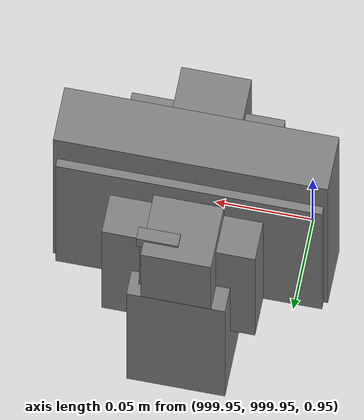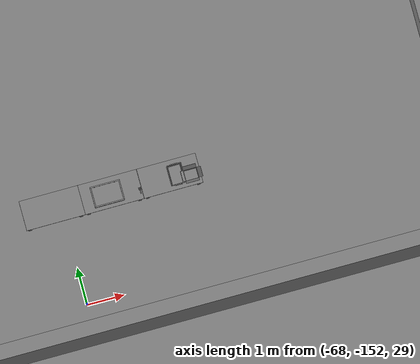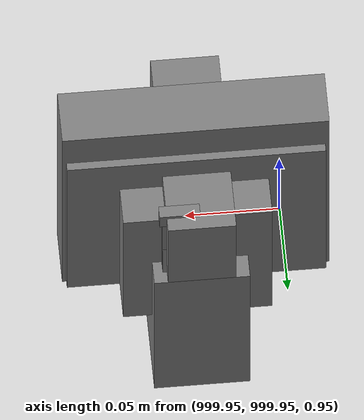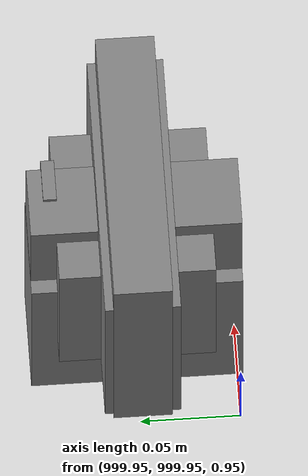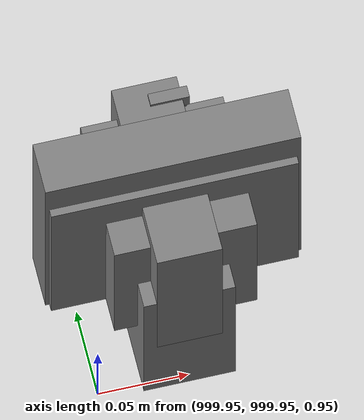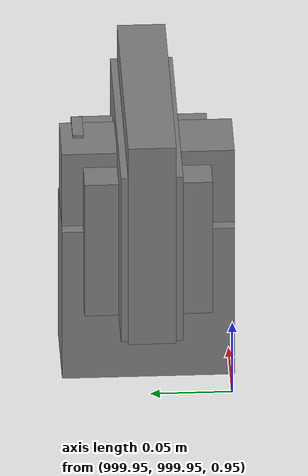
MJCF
<mujoco>
    <option gravity="0.000000000 0.000000000 -9.810000420" timestep="0.0049999999" integrator="implicitfast" density="1.225" viscosity="1.8000001e-05" noslip_iterations="10" iterations="100" sdf_iterations="50">
        <flag multiccd="disable"/>
    </option>
    <size memory="1000M"/>
    <compiler coordinate="local"/>
    <worldbody>
        <light cutoff="30" pos="0 1 1" dir="0 -1 -2"/>
        <light cutoff="30" pos="0 -1 1" dir="0 1 -2"/>
        <body pos="1000.000000000 1000.000000000 1.000000000" euler="0.000000000 0.000000000 180.000000000" name="openloong_gripper_2f85_fix_base_usda_battery_01">
            <geom contype="1" conaffinity="1" density="1000" type="box" material="" rgba="0.500000000 0.500000000 0.500000000 1.000000000" solimp="0.899999976 0.949999988 0.001000000" friction="1.000000000 0.005000000 0.000100000" solref="0.020000000 1.000000000" margin="0" condim="3" group="0" pos="-0.011123657 -0.041940309 0.101691343" quat="1.000000000 0.000000000 0.000000000 0.000000000" size="0.010800000 0.003375000 0.004725000" name="openloong_gripper_2f85_fix_base_usda_geom_5E2F86DE_207D_4490_AB18_F2192BC1EB1F"/>
            <geom contype="1" conaffinity="1" density="1000" type="box" material="" rgba="0.500000000 0.500000000 0.500000000 1.000000000" solimp="0.899999976 0.949999988 0.001000000" friction="1.000000000 0.005000000 0.000100000" solref="0.020000000 1.000000000" margin="0" condim="3" group="0" pos="-0.010876465 -0.044247437 0.047066893" quat="0.998702705 -0.050920475 0.000000000 0.000000000" size="0.009450001 0.002700000 0.024975000" name="openloong_gripper_2f85_fix_base_usda_geom_F8554C31_2C14_4601_B655_FA4A322580DE"/>
            <geom contype="1" conaffinity="1" density="1000" type="box" material="" rgba="0.500000000 0.500000000 0.500000000 1.000000000" solimp="0.899999976 0.949999988 0.001000000" friction="1.000000000 0.005000000 0.000100000" solref="0.020000000 1.000000000" margin="0" condim="3" group="0" pos="-0.001235962 -0.000659180 0.047381196" quat="1.000000000 0.000000000 0.000000000 0.000000000" size="0.039420001 0.039150000 0.047250003" name="openloong_gripper_2f85_fix_base_usda_geom_7E45CB5D_F0DA_4121_990F_6D450E5E1EEE"/>
            <geom contype="1" conaffinity="1" density="1000" type="box" material="" rgba="0.500000000 0.500000000 0.500000000 1.000000000" solimp="0.899999976 0.949999988 0.001000000" friction="1.000000000 0.005000000 0.000100000" solref="0.020000000 1.000000000" margin="0" condim="3" group="0" pos="-0.010876465 -0.039138794 0.009851727" quat="1.000000000 0.000000000 0.000000000 0.000000000" size="0.009450001 0.010800000 0.013500000" name="openloong_gripper_2f85_fix_base_usda_geom_0261A3B7_262F_45EE_A699_6ED76B3A2211"/>
            <geom contype="1" conaffinity="1" density="1000" type="box" material="" rgba="0.500000000 0.500000000 0.500000000 1.000000000" solimp="0.899999976 0.949999988 0.001000000" friction="1.000000000 0.005000000 0.000100000" solref="0.020000000 1.000000000" margin="0" condim="3" group="0" pos="-0.010876465 -0.041528322 0.071508206" quat="1.000000000 0.000000000 0.000000000 0.000000000" size="0.009450001 0.002700000 0.027000001" name="openloong_gripper_2f85_fix_base_usda_geom_43187129_42B7_4759_A2D2_8282421862A7"/>
            <freejoint name="openloong_gripper_2f85_fix_base_usda_battery_01_joint"/>
            <site size="0.005000000 0.005000000 0.005000000" rgba="0.500000000 0.500000000 0.500000000 1.000000000" pos="0.000000000 0.000000000 0.000000000" quat="0.999961913 0.008726500 0.000000000 0.000000000" group="0" type="sphere" name="openloong_gripper_2f85_fix_base_usda_battery_01site"/>
        </body>
        <body pos="-66.388343811 -149.571334839 31.170923233" euler="-99.366661072 5.741098881 -143.393768311" mocap="true" name="spotlight3_SpotLight"/>
        <body pos="1000.000000000 1000.000000000 1.000000000" euler="0.000000000 0.000000000 180.000000000" name="openloong_gripper_2f85_fix_base_usda_cpu_fan">
            <geom contype="1" conaffinity="1" density="1000" type="box" material="" rgba="0.500000000 0.500000000 0.500000000 1.000000000" solimp="0.899999976 0.949999988 0.001000000" friction="1.000000000 0.005000000 0.000100000" solref="0.020000000 1.000000000" margin="0" condim="3" group="0" pos="0.000000000 0.000000000 0.070034981" quat="0.000000000 0.000000000 0.000000000 1.000000000" size="0.070700005 0.014699999 0.070700005" name="openloong_gripper_2f85_fix_base_usda_geom_A22CB827_F862_4CD4_8335_74C05EDA61AA"/>
            <freejoint name="openloong_gripper_2f85_fix_base_usda_cpu_fan_joint"/>
            <site size="0.005000000 0.005000000 0.005000000" rgba="0.500000000 0.500000000 0.500000000 1.000000000" pos="0.000000000 0.000000000 0.000000000" quat="0.999961913 0.008726535 0.000000000 0.000000000" group="0" type="sphere" name="openloong_gripper_2f85_fix_base_usda_cpu_fancsite"/>
        </body>
        <body pos="1000.000000000 1000.000000000 1.000000000" euler="0.000000000 0.000000000 180.000000000" name="openloong_gripper_2f85_fix_base_usda_wifi_box">
            <geom contype="1" conaffinity="1" density="1000" type="box" material="" rgba="0.500000000 0.500000000 0.500000000 1.000000000" solimp="0.899999976 0.949999988 0.001000000" friction="1.000000000 0.005000000 0.000100000" solref="0.020000000 1.000000000" margin="0" condim="3" group="0" pos="0.000000000 0.000000000 0.058978677" quat="0.000000000 0.000000047 0.000000000 1.000000000" size="0.068499997 0.018999999 0.059000000" name="openloong_gripper_2f85_fix_base_usda_geom_A910E36D_3049_475C_8AEA_D618EE6DB76B"/>
            <freejoint name="openloong_gripper_2f85_fix_base_usda_wifi_box_joint"/>
            <site size="0.005000000 0.005000000 0.005000000" rgba="0.500000000 0.500000000 0.500000000 1.000000000" pos="0.000000000 0.000000000 0.000000000" quat="0.999961913 0.008726500 0.000000000 0.000000000" group="0" type="sphere" name="openloong_gripper_2f85_fix_base_usda_wifi_boxsite"/>
        </body>
        <body pos="1000.000000000 1000.000000000 1.000000000" euler="0.000011953 0.000005123 -179.999984741" name="openloong_gripper_2f85_fix_base_usda_intel_box">
            <geom contype="1" conaffinity="1" density="1000" type="box" material="" rgba="0.500000000 0.500000000 0.500000000 1.000000000" solimp="0.899999976 0.949999988 0.001000000" friction="1.000000000 0.005000000 0.000100000" solref="0.020000000 1.000000000" margin="0" condim="3" group="0" pos="0.000000000 -0.000067139 0.000082284" quat="0.707106709 0.000000225 0.000000253 0.707106650" size="0.052800003 0.025300000 0.052800003" name="openloong_gripper_2f85_fix_base_usda_geom_CD061FAA_8896_4456_9F66_24A22E8AD5FD"/>
            <freejoint name="openloong_gripper_2f85_fix_base_usda_intel_box_joint"/>
            <site size="0.005000000 0.005000000 0.005000000" rgba="0.500000000 0.500000000 0.500000000 1.000000000" pos="0.000000000 0.000000000 0.000000000" quat="0.999961913 0.008726500 0.000000000 0.000000000" group="0" type="sphere" name="openloong_gripper_2f85_fix_base_usda_intel_boxsite"/>
        </body>
        <body pos="1000.000000000 999.999938965 1.000000000" euler="0.000000000 0.000000000 180.000000000" name="openloong_gripper_2f85_fix_base_usda_intelcore_i5">
            <geom contype="1" conaffinity="1" density="1000" type="box" material="" rgba="0.500000000 0.500000000 0.500000000 1.000000000" solimp="0.899999976 0.949999988 0.001000000" friction="1.000000000 0.005000000 0.000100000" solref="0.020000000 1.000000000" margin="0" condim="3" group="0" pos="0.000000000 0.000000000 0.051722717" quat="0.707106709 0.000000000 0.000000000 -0.707106769" size="0.052800000 0.018080002 0.052800000" name="openloong_gripper_2f85_fix_base_usda_geom_3D3FF9B1_32B9_488A_9E04_4B020A0D96EA"/>
            <freejoint name="openloong_gripper_2f85_fix_base_usda_intelcore_i5_joint"/>
            <site size="0.005000000 0.005000000 0.005000000" rgba="0.500000000 0.500000000 0.500000000 1.000000000" pos="0.000000000 0.000000000 0.000000000" quat="0.999961913 0.008726534 0.000000000 0.000000000" group="0" type="sphere" name="openloong_gripper_2f85_fix_base_usda_intelcore_i5site"/>
        </body>
        <body pos="-66.002174377 -149.263900757 31.169902802" euler="114.549728394 -34.595951080 85.069427490" mocap="true" name="spotlight2_SpotLight"/>
        <body pos="-66.351432800 -148.898254395 31.165010452" euler="128.671417236 -18.958011627 98.540748596" mocap="true" name="spotlight1_SpotLight"/>
        <body pos="-64.866622925 -149.383972168 30.183746338" euler="89.999984741 89.999946594 0.000000000" name="openloong_gripper_2f85_fix_base_usda_bluebox_01">
            <geom contype="1" conaffinity="1" density="1000" type="box" material="" rgba="0.500000000 0.500000000 0.500000000 1.000000000" solimp="0.899999976 0.949999988 0.001000000" friction="1.000000000 0.005000000 0.000100000" solref="0.020000000 1.000000000" margin="0" condim="3" group="0" pos="0.276580811 0.187225342 0.000068665" quat="0.707106948 0.000077471 0.707106352 0.000077486" size="0.100000001 0.057999998 0.010000000" name="openloong_gripper_2f85_fix_base_usda_geom_7BDD5228_270B_486F_85F2_97819AC2F21C"/>
            <geom contype="1" conaffinity="1" density="1000" type="box" material="" rgba="0.500000000 0.500000000 0.500000000 1.000000000" solimp="0.899999976 0.949999988 0.001000000" friction="1.000000000 0.005000000 0.000100000" solref="0.020000000 1.000000000" margin="0" condim="3" group="0" pos="0.000000000 0.002883911 0.000000000" quat="0.999999881 0.000000000 0.000000000 0.000000000" size="0.254000008 0.003000000 0.172000006" name="openloong_gripper_2f85_fix_base_usda_geom_CEA9F2AF_9288_46AA_AD6E_57079D07113B"/>
            <geom contype="1" conaffinity="1" density="1000" type="box" material="" rgba="0.500000000 0.500000000 0.500000000 1.000000000" solimp="0.899999976 0.949999988 0.001000000" friction="1.000000000 0.005000000 0.000100000" solref="0.020000000 1.000000000" margin="0" condim="3" group="0" pos="0.000000000 0.124874115 0.173484802" quat="0.999796331 0.020176515 -0.000000015 0.000000030" size="0.259999990 0.119999997 0.007000000" name="openloong_gripper_2f85_fix_base_usda_geom_48E2AEB2_A364_49A8_AD1E_BD6E6F5C290E"/>
            <geom contype="1" conaffinity="1" density="1000" type="box" material="" rgba="0.500000000 0.500000000 0.500000000 1.000000000" solimp="0.899999976 0.949999988 0.001000000" friction="1.000000000 0.005000000 0.000100000" solref="0.020000000 1.000000000" margin="0" condim="3" group="0" pos="0.000000000 0.124874115 -0.173469543" quat="0.999796331 -0.020176545 -0.000000015 0.000000000" size="0.259999990 0.119999997 0.007000000" name="openloong_gripper_2f85_fix_base_usda_geom_9DAAEF2C_C035_4BFF_AD85_68047CB8894D"/>
            <geom contype="1" conaffinity="1" density="1000" type="box" material="" rgba="0.500000000 0.500000000 0.500000000 1.000000000" solimp="0.899999976 0.949999988 0.001000000" friction="1.000000000 0.005000000 0.000100000" solref="0.020000000 1.000000000" margin="0" condim="3" group="0" pos="0.000000000 0.214008331 0.188980103" quat="0.999912977 0.013176724 0.000000015 0.000000000" size="0.259999990 0.029999999 0.012500000" name="openloong_gripper_2f85_fix_base_usda_geom_363570C8_4A9E_4171_A21A_4AEFF0CA8895"/>
            <geom contype="1" conaffinity="1" density="1000" type="box" material="" rgba="0.500000000 0.500000000 0.500000000 1.000000000" solimp="0.899999976 0.949999988 0.001000000" friction="1.000000000 0.005000000 0.000100000" solref="0.020000000 1.000000000" margin="0" condim="3" group="0" pos="-0.258361816 0.125289917 0.001876831" quat="0.702796936 -0.020792112 0.710783124 0.020769298" size="0.189999998 0.119999997 0.009000000" name="openloong_gripper_2f85_fix_base_usda_geom_9FDD9A62_FA75_4254_AC16_001CC357A119"/>
            <geom contype="1" conaffinity="1" density="1000" type="box" material="" rgba="0.500000000 0.500000000 0.500000000 1.000000000" solimp="0.899999976 0.949999988 0.001000000" friction="1.000000000 0.005000000 0.000100000" solref="0.020000000 1.000000000" margin="0" condim="3" group="0" pos="0.000000000 0.214008331 -0.188980103" quat="0.999912977 -0.013176769 0.000000030 0.000000015" size="0.259999990 0.029999999 0.012500000" name="openloong_gripper_2f85_fix_base_usda_geom_F312884E_29F6_4E55_912C_7BC0AFFF8E3A"/>
            <geom contype="1" conaffinity="1" density="1000" type="box" material="" rgba="0.500000000 0.500000000 0.500000000 1.000000000" solimp="0.899999976 0.949999988 0.001000000" friction="1.000000000 0.005000000 0.000100000" solref="0.020000000 1.000000000" margin="0" condim="3" group="0" pos="-0.276611328 0.187225342 0.000068665" quat="0.707106650 0.000077441 0.707106709 0.000077456" size="0.100000001 0.057999998 0.010000000" name="openloong_gripper_2f85_fix_base_usda_geom_FB988E8A_CEE7_4890_B753_8F08CA714F1D"/>
            <geom contype="1" conaffinity="1" density="1000" type="box" material="" rgba="0.500000000 0.500000000 0.500000000 1.000000000" solimp="0.899999976 0.949999988 0.001000000" friction="1.000000000 0.005000000 0.000100000" solref="0.020000000 1.000000000" margin="0" condim="3" group="0" pos="0.258331299 0.125289917 0.001876831" quat="0.702851415 0.018856421 0.710823774 -0.019329369" size="0.189999998 0.119999997 0.009000000" name="openloong_gripper_2f85_fix_base_usda_geom_E6748F7D_07E5_4A98_8A90_E9A79DBA282E"/>
            <freejoint name="openloong_gripper_2f85_fix_base_usda_bluebox_01_joint"/>
            <site size="0.005000000 0.005000000 0.005000000" rgba="0.500000000 0.500000000 0.500000000 1.000000000" pos="0.000000000 0.000000000 0.000000000" quat="0.999961913 0.008726534 0.000000000 0.000000000" group="0" type="sphere" name="openloong_gripper_2f85_fix_base_usda_bluebox_01site"/>
        </body>
        <body pos="-64.496299744 -149.491867065 30.235729218" euler="0.000000000 0.000000000 89.999946594" name="openloong_gripper_2f85_fix_base_usda_cardboardbox_01">
            <geom contype="1" conaffinity="1" density="1000" type="box" material="" rgba="0.500000000 0.500000000 0.500000000 1.000000000" solimp="0.899999976 0.949999988 0.001000000" friction="1.000000000 0.005000000 0.000100000" solref="0.020000000 1.000000000" margin="0" condim="3" group="0" pos="-0.003166199 -0.004086494 0.005052090" quat="1.000000000 0.000000000 0.000000000 0.000000000" size="0.142499998 0.177500010 0.005000000" name="openloong_gripper_2f85_fix_base_usda_geom_D468F566_DD48_4998_A7B3_2FBA2E0B5360"/>
            <geom contype="1" conaffinity="1" density="1000" type="box" material="" rgba="0.500000000 0.500000000 0.500000000 1.000000000" solimp="0.899999976 0.949999988 0.001000000" friction="1.000000000 0.005000000 0.000100000" solref="0.020000000 1.000000000" margin="0" condim="3" group="0" pos="-0.003166199 0.170316696 0.150570869" quat="1.000000000 0.000000000 0.000000000 0.000000000" size="0.142499998 0.005000000 0.149999991" name="openloong_gripper_2f85_fix_base_usda_geom_88742ACB_2144_4A79_9BB6_715A09679380"/>
            <geom contype="1" conaffinity="1" density="1000" type="box" material="" rgba="0.500000000 0.500000000 0.500000000 1.000000000" solimp="0.899999976 0.949999988 0.001000000" friction="1.000000000 0.005000000 0.000100000" solref="0.020000000 1.000000000" margin="0" condim="3" group="0" pos="-0.147399902 -0.005307198 0.150570869" quat="1.000000000 0.000000000 0.000000000 0.000000000" size="0.005000000 0.177500010 0.149999991" name="openloong_gripper_2f85_fix_base_usda_geom_934A3255_22C3_4E4E_9995_85ECEA2250DB"/>
            <geom contype="1" conaffinity="1" density="1000" type="box" material="" rgba="0.500000000 0.500000000 0.500000000 1.000000000" solimp="0.899999976 0.949999988 0.001000000" friction="1.000000000 0.005000000 0.000100000" solref="0.020000000 1.000000000" margin="0" condim="3" group="0" pos="0.140275955 -0.005307198 0.150570869" quat="1.000000000 0.000000000 0.000000000 0.000000000" size="0.005000000 0.177500010 0.149999991" name="openloong_gripper_2f85_fix_base_usda_geom_631CD57D_E9CE_41B1_9763_BB90DB6A8491"/>
            <geom contype="1" conaffinity="1" density="1000" type="box" material="" rgba="0.500000000 0.500000000 0.500000000 1.000000000" solimp="0.899999976 0.949999988 0.001000000" friction="1.000000000 0.005000000 0.000100000" solref="0.020000000 1.000000000" margin="0" condim="3" group="0" pos="-0.003166199 -0.181550980 0.150570869" quat="1.000000000 0.000000000 0.000000000 0.000000000" size="0.142499998 0.005000000 0.149999991" name="openloong_gripper_2f85_fix_base_usda_geom_A2E52CDE_2255_4B59_BF21_02ABA828E415"/>
            <freejoint name="openloong_gripper_2f85_fix_base_usda_cardboardbox_01_joint"/>
            <site size="0.005000000 0.005000000 0.005000000" rgba="0.500000000 0.500000000 0.500000000 1.000000000" pos="0.000000000 0.000000000 0.000000000" quat="0.999961913 0.008726535 0.000000000 0.000000000" group="0" type="sphere" name="openloong_gripper_2f85_fix_base_usda_site_07E03E1A_A894_4603_BD9F_5575C8D9489E"/>
            <body pos="0.139160156 -0.004048347 0.301930904" euler="-179.999954224 49.383502960 179.999954224" name="openloong_gripper_2f85_fix_base_usda_A1_006">
                <geom contype="1" conaffinity="1" density="1000" type="box" material="" rgba="0.500000000 0.500000000 0.500000000 1.000000000" solimp="0.899999976 0.949999988 0.001000000" friction="1.000000000 0.005000000 0.000100000" solref="0.020000000 1.000000000" margin="0" condim="3" group="0" pos="-0.071587563 0.000009537 0.001745224" quat="0.999999881 0.000000000 0.000000000 0.000000000" size="0.071249999 0.179999992 0.002500000" name="openloong_gripper_2f85_fix_base_usda_geom_0BEED558_5F25_4605_96D6_65224B2D2F0F"/>
                <joint armature="0" stiffness="0.07" damping="0.0099999998" axis="0.000000 1.000000 0.000000" type="hinge" name="openloong_gripper_2f85_fix_base_usda_A1_006"/>
            </body>
            <body pos="-0.145902634 -0.004086494 0.301938057" euler="-180.000000000 -60.000011444 -180.000000000" name="openloong_gripper_2f85_fix_base_usda_A2_006">
                <geom contype="1" conaffinity="1" density="1000" type="box" material="" rgba="0.500000000 0.500000000 0.500000000 1.000000000" solimp="0.899999976 0.949999988 0.001000000" friction="1.000000000 0.005000000 0.000100000" solref="0.020000000 1.000000000" margin="0" condim="3" group="0" pos="0.071268082 0.000009537 0.002717972" quat="0.000002921 0.000000000 -0.000000030 0.999999881" size="0.071249999 0.179999992 0.002500000" name="openloong_gripper_2f85_fix_base_usda_geom_15DA7C9E_2443_4902_B6F9_79B9D0D5C203"/>
                <joint armature="0" stiffness="0.07" damping="0.0099999998" axis="0.000000 1.000000 0.000000" type="hinge" name="openloong_gripper_2f85_fix_base_usda_A2_006"/>
            </body>
            <body pos="-0.003385544 0.175991058 0.301930904" euler="-125.858116150 -0.000004561 0.000002331" name="openloong_gripper_2f85_fix_base_usda_B2_006">
                <geom contype="1" conaffinity="1" density="1000" type="box" material="" rgba="0.500000000 0.500000000 0.500000000 1.000000000" solimp="0.899999976 0.949999988 0.001000000" friction="1.000000000 0.005000000 0.000100000" solref="0.020000000 1.000000000" margin="0" condim="3" group="0" pos="0.000009537 -0.070939064 -0.002470016" quat="0.999614120 0.027776197 -0.000000015 0.000000030" size="0.137500003 0.064999998 0.005000000" name="openloong_gripper_2f85_fix_base_usda_geom_8D27F73F_D3F9_4795_9155_97D4571A3986"/>
                <joint armature="0" stiffness="0.07" damping="0.0099999998" axis="1.000000 0.000000 0.000000" type="hinge" name="openloong_gripper_2f85_fix_base_usda_B2_006"/>
            </body>
            <body pos="-0.003385544 -0.184140205 0.301938057" euler="147.805557251 0.000000000 0.000000000" name="openloong_gripper_2f85_fix_base_usda_B1_006">
                <geom contype="1" conaffinity="1" density="1000" type="box" material="" rgba="0.500000000 0.500000000 0.500000000 1.000000000" solimp="0.899999976 0.949999988 0.001000000" friction="1.000000000 0.005000000 0.000100000" solref="0.020000000 1.000000000" margin="0" condim="3" group="0" pos="-0.000028610 0.070202351 -0.002703667" quat="0.999614179 -0.027776167 0.000000000 0.000000000" size="0.137500003 0.064999998 0.005000000" name="openloong_gripper_2f85_fix_base_usda_geom_5DE69AD0_7271_4657_A080_B7574C4AC2C3"/>
                <joint armature="0" stiffness="0.07" damping="0.0099999998" axis="1.000000 0.000000 0.000000" type="hinge" name="openloong_gripper_2f85_fix_base_usda_B1_006"/>
            </body>
        </body>
        <body pos="-65.882858276 -149.481979370 30.229999542" euler="-64.487716675 0.000000000 0.000000000" name="openloong_gripper_2f85_fix_base_usda_Barcode">
            <geom contype="1" conaffinity="1" density="1000" type="box" material="" rgba="0.500000000 0.500000000 0.500000000 1.000000000" solimp="0.899999976 0.949999988 0.001000000" friction="1.000000000 0.005000000 0.000100000" solref="0.020000000 1.000000000" margin="0" condim="3" group="0" pos="0.000000000 0.013038635 0.001419067" quat="0.000000000 0.000000000 0.000000000 1.000000119" size="0.034000002 0.010000000 0.017999999" name="openloong_gripper_2f85_fix_base_usda_geom_AEEB8E12_7B17_4BA8_B8A5_AB8D91572C91"/>
            <geom contype="1" conaffinity="1" density="1000" type="box" material="" rgba="0.500000000 0.500000000 0.500000000 1.000000000" solimp="0.899999976 0.949999988 0.001000000" friction="1.000000000 0.005000000 0.000100000" solref="0.020000000 1.000000000" margin="0" condim="3" group="0" pos="0.000000000 -0.035301208 -0.007095337" quat="0.000000000 0.000000000 -0.043619365 0.999048233" size="0.028999999 0.010000000 0.020000000" name="openloong_gripper_2f85_fix_base_usda_geom_2E356133_9F91_4BD5_99DC_53DD349B06A6"/>
            <geom contype="1" conaffinity="1" density="1000" type="box" material="" rgba="0.500000000 0.500000000 0.500000000 1.000000000" solimp="0.899999976 0.949999988 0.001000000" friction="1.000000000 0.005000000 0.000100000" solref="0.020000000 1.000000000" margin="0" condim="3" group="0" pos="0.000000000 -0.043411255 -0.011749268" quat="0.922262907 0.386563420 0.000000000 0.000000000" size="0.026000001 0.010000000 0.020000000" name="openloong_gripper_2f85_fix_base_usda_geom_7073419D_CA23_4DB9_9431_AB0836396D13"/>
            <geom contype="1" conaffinity="1" density="1000" type="box" material="" rgba="0.500000000 0.500000000 0.500000000 1.000000000" solimp="0.899999976 0.949999988 0.001000000" friction="1.000000000 0.005000000 0.000100000" solref="0.020000000 1.000000000" margin="0" condim="3" group="0" pos="0.000000000 -0.016967773 -0.031860352" quat="0.000000000 0.000000000 0.000000000 1.000000119" size="0.008000000 0.010000000 0.013000000" name="openloong_gripper_2f85_fix_base_usda_geom_E37FC0BC_5498_4AFC_A982_5F13FD5FD289"/>
            <geom contype="1" conaffinity="1" density="1000" type="box" material="" rgba="0.500000000 0.500000000 0.500000000 1.000000000" solimp="0.899999976 0.949999988 0.001000000" friction="1.000000000 0.005000000 0.000100000" solref="0.020000000 1.000000000" margin="0" condim="3" group="0" pos="0.000000000 -0.001869202 0.000312805" quat="0.953716993 0.300705761 0.000000000 0.000000000" size="0.032000002 0.010000000 0.018999999" name="openloong_gripper_2f85_fix_base_usda_geom_816F3AE6_99F4_4C4C_BDF5_09C9AFAD2221"/>
            <geom contype="1" conaffinity="1" density="1000" type="box" material="" rgba="0.500000000 0.500000000 0.500000000 1.000000000" solimp="0.899999976 0.949999988 0.001000000" friction="1.000000000 0.005000000 0.000100000" solref="0.020000000 1.000000000" margin="0" condim="3" group="0" pos="0.000000000 -0.019531250 -0.003173828" quat="0.953716993 0.300705761 0.000000000 0.000000000" size="0.030999999 0.010000000 0.020000000" name="openloong_gripper_2f85_fix_base_usda_geom_1709738F_82BD_4FBF_9A0B_C081FBBC1FC8"/>
            <geom contype="1" conaffinity="1" density="1000" type="box" material="" rgba="0.500000000 0.500000000 0.500000000 1.000000000" solimp="0.899999976 0.949999988 0.001000000" friction="1.000000000 0.005000000 0.000100000" solref="0.020000000 1.000000000" margin="0" condim="3" group="0" pos="0.000000000 -0.035301208 -0.007095337" quat="0.953716993 0.300705761 0.000000000 0.000000000" size="0.028999999 0.010000000 0.020000000" name="openloong_gripper_2f85_fix_base_usda_geom_255560C2_24F1_41B2_8BCF_A2CC465E83C8"/>
            <geom contype="1" conaffinity="1" density="1000" type="box" material="" rgba="0.500000000 0.500000000 0.500000000 1.000000000" solimp="0.899999976 0.949999988 0.001000000" friction="1.000000000 0.005000000 0.000100000" solref="0.020000000 1.000000000" margin="0" condim="3" group="0" pos="0.000000000 -0.042617798 -0.071121216" quat="0.000000000 0.000000000 0.000000000 1.000000119" size="0.013000000 0.021000000 0.059999999" name="openloong_gripper_2f85_fix_base_usda_geom_F165540E_7764_4239_ADD4_5C8801AF495A"/>
            <freejoint name="openloong_gripper_2f85_fix_base_usda_Barcode_joint"/>
            <site size="0.005000000 0.005000000 0.005000000" rgba="0.500000000 0.500000000 0.500000000 1.000000000" pos="0.000000000 0.000000000 0.000000000" quat="1.000000000 0.000000000 0.000000000 0.000000000" group="0" type="sphere" name="openloong_gripper_2f85_fix_base_usda_Barcode_site"/>
        </body>
        <body pos="-66.745018005 -149.392349243 30.184000015" euler="0.000000000 0.000000000 89.999946594" name="[22333007846429]_Basket_01">
            <geom contype="1" conaffinity="1" density="1000" type="box" material="" rgba="0.500000000 0.500000000 0.500000000 1.000000000" solimp="0.899999976 0.949999988 0.001000000" friction="1.000000000 0.005000000 0.000100000" solref="0.020000000 1.000000000" margin="0" condim="3" group="0" pos="-0.052425385 0.389207840 0.089787483" quat="0.707107008 0.000000000 0.000000000 0.707106411" size="0.014249999 0.014249999 0.059999999" name="[22333007846429]_geom_35221AF5_8D3D_4EAB_8A4F_5EC2217266B1"/>
            <geom contype="1" conaffinity="1" density="1000" type="box" material="" rgba="0.500000000 0.500000000 0.500000000 1.000000000" solimp="0.899999976 0.949999988 0.001000000" friction="1.000000000 0.005000000 0.000100000" solref="0.020000000 1.000000000" margin="0" condim="3" group="0" pos="0.264015198 -0.133043289 0.089787483" quat="0.707107008 0.000000000 0.000000000 0.707106411" size="0.014249999 0.014249999 0.059999999" name="[22333007846429]_geom_EF183E53_FEAC_465C_833A_0E5FEC78D077"/>
            <geom contype="1" conaffinity="1" density="1000" type="box" material="" rgba="0.500000000 0.500000000 0.500000000 1.000000000" solimp="0.899999976 0.949999988 0.001000000" friction="1.000000000 0.005000000 0.000100000" solref="0.020000000 1.000000000" margin="0" condim="3" group="0" pos="-0.264015198 -0.265548706 0.089793205" quat="0.707107008 0.000000000 0.000000000 0.707106411" size="0.014249999 0.014249999 0.059999999" name="[22333007846429]_geom_0D9C7039_220E_45AC_95D0_25453B60C8F7"/>
            <geom contype="1" conaffinity="1" density="1000" type="box" material="" rgba="0.500000000 0.500000000 0.500000000 1.000000000" solimp="0.899999976 0.949999988 0.001000000" friction="1.000000000 0.005000000 0.000100000" solref="0.020000000 1.000000000" margin="0" condim="3" group="0" pos="-0.160263062 -0.389322281 0.089793205" quat="0.707107008 0.000000000 0.000000000 0.707106411" size="0.014249999 0.014249999 0.059999999" name="[22333007846429]_geom_1826F0B5_16ED_4132_B7D7_DA74161FC504"/>
            <geom contype="1" conaffinity="1" density="1000" type="box" material="" rgba="0.500000000 0.500000000 0.500000000 1.000000000" solimp="0.899999976 0.949999988 0.001000000" friction="1.000000000 0.005000000 0.000100000" solref="0.020000000 1.000000000" margin="0" condim="3" group="0" pos="0.162265778 -0.389322281 0.089787483" quat="0.707107008 0.000000000 0.000000000 0.707106411" size="0.014249999 0.014249999 0.059999999" name="[22333007846429]_geom_58027C54_1278_42DB_AF63_5050667763F2"/>
            <geom contype="1" conaffinity="1" density="1000" type="box" material="" rgba="0.500000000 0.500000000 0.500000000 1.000000000" solimp="0.899999976 0.949999988 0.001000000" friction="1.000000000 0.005000000 0.000100000" solref="0.020000000 1.000000000" margin="0" condim="3" group="0" pos="0.264015198 0.389207840 0.089787483" quat="0.707107008 0.000000000 0.000000000 0.707106411" size="0.014249999 0.014249999 0.059999999" name="[22333007846429]_geom_DDB0BBAA_6D82_4F49_9401_79C6D3DECDCF"/>
            <geom contype="1" conaffinity="1" density="1000" type="box" material="" rgba="0.500000000 0.500000000 0.500000000 1.000000000" solimp="0.899999976 0.949999988 0.001000000" friction="1.000000000 0.005000000 0.000100000" solref="0.020000000 1.000000000" margin="0" condim="3" group="0" pos="-0.264015198 -0.133043289 0.089793205" quat="0.707107008 0.000000000 0.000000000 0.707106411" size="0.014249999 0.014249999 0.059999999" name="[22333007846429]_geom_226CD08E_4083_4BE9_BA80_B830E1BCE78C"/>
            <geom contype="1" conaffinity="1" density="1000" type="box" material="" rgba="0.500000000 0.500000000 0.500000000 1.000000000" solimp="0.899999976 0.949999988 0.001000000" friction="1.000000000 0.005000000 0.000100000" solref="0.020000000 1.000000000" margin="0" condim="3" group="0" pos="-0.264026642 0.269256592 0.089793205" quat="0.707107008 0.000000000 0.000000000 0.707106411" size="0.014249999 0.014249999 0.059999999" name="[22333007846429]_geom_7A38EA30_4833_4284_8DE5_EB36D5F71D24"/>
            <geom contype="1" conaffinity="1" density="1000" type="box" material="" rgba="0.500000000 0.500000000 0.500000000 1.000000000" solimp="0.899999976 0.949999988 0.001000000" friction="1.000000000 0.005000000 0.000100000" solref="0.020000000 1.000000000" margin="0" condim="3" group="0" pos="0.054462433 0.389207840 0.089787483" quat="0.707107008 0.000000000 0.000000000 0.707106411" size="0.014249999 0.014249999 0.059999999" name="[22333007846429]_geom_CDD80510_A461_425A_A569_3F97FF111479"/>
            <geom contype="1" conaffinity="1" density="1000" type="box" material="" rgba="0.500000000 0.500000000 0.500000000 1.000000000" solimp="0.899999976 0.949999988 0.001000000" friction="1.000000000 0.005000000 0.000100000" solref="0.020000000 1.000000000" margin="0" condim="3" group="0" pos="0.054462433 -0.389322281 0.089787483" quat="0.707107008 0.000000000 0.000000000 0.707106411" size="0.014249999 0.014249999 0.059999999" name="[22333007846429]_geom_0DBBBD9F_739D_4BB7_AC7C_5DA31A01BDDD"/>
            <geom contype="1" conaffinity="1" density="1000" type="box" material="" rgba="0.500000000 0.500000000 0.500000000 1.000000000" solimp="0.899999976 0.949999988 0.001000000" friction="1.000000000 0.005000000 0.000100000" solref="0.020000000 1.000000000" margin="0" condim="3" group="0" pos="0.264015198 0.269256592 0.089793205" quat="0.707107008 0.000000000 0.000000000 0.707106411" size="0.014249999 0.014249999 0.059999999" name="[22333007846429]_geom_67669858_F47D_4CD4_AB4E_EA2AB0D32CB5"/>
            <geom contype="1" conaffinity="1" density="1000" type="box" material="" rgba="0.500000000 0.500000000 0.500000000 1.000000000" solimp="0.899999976 0.949999988 0.001000000" friction="1.000000000 0.005000000 0.000100000" solref="0.020000000 1.000000000" margin="0" condim="3" group="0" pos="0.264015198 -0.389322281 0.089787483" quat="0.707107008 0.000000000 0.000000000 0.707106411" size="0.014249999 0.014249999 0.059999999" name="[22333007846429]_geom_61957AA4_410C_47EC_BCFD_1DDC5AE55412"/>
            <geom contype="1" conaffinity="1" density="1000" type="box" material="" rgba="0.500000000 0.500000000 0.500000000 1.000000000" solimp="0.899999976 0.949999988 0.001000000" friction="1.000000000 0.005000000 0.000100000" solref="0.020000000 1.000000000" margin="0" condim="3" group="0" pos="0.000000000 0.000000000 0.015998840" quat="0.707107008 0.000000000 0.000000000 0.707106411" size="0.403499991 0.279000014 0.015750000" name="[22333007846429]_geom_7BEFE3B4_57CA_4FC6_82CD_08F7E452DD4C"/>
            <geom contype="1" conaffinity="1" density="1000" type="box" material="" rgba="0.500000000 0.500000000 0.500000000 1.000000000" solimp="0.899999976 0.949999988 0.001000000" friction="1.000000000 0.005000000 0.000100000" solref="0.020000000 1.000000000" margin="0" condim="3" group="0" pos="0.000000000 -0.389476776 0.163619041" quat="0.707107008 0.000000000 0.000000000 0.707106411" size="0.015000000 0.277500004 0.015750000" name="[22333007846429]_geom_43357AEB_398E_423F_A333_EF562F4858E4"/>
            <geom contype="1" conaffinity="1" density="1000" type="box" material="" rgba="0.500000000 0.500000000 0.500000000 1.000000000" solimp="0.899999976 0.949999988 0.001000000" friction="1.000000000 0.005000000 0.000100000" solref="0.020000000 1.000000000" margin="0" condim="3" group="0" pos="0.162265778 0.389207840 0.089787483" quat="0.707107008 0.000000000 0.000000000 0.707106411" size="0.014249999 0.014249999 0.059999999" name="[22333007846429]_geom_FD702416_05AE_483A_A531_CE0E31C762D0"/>
            <geom contype="1" conaffinity="1" density="1000" type="box" material="" rgba="0.500000000 0.500000000 0.500000000 1.000000000" solimp="0.899999976 0.949999988 0.001000000" friction="1.000000000 0.005000000 0.000100000" solref="0.020000000 1.000000000" margin="0" condim="3" group="0" pos="0.000000000 0.389471054 0.163619041" quat="0.707107008 0.000000000 0.000000000 0.707106411" size="0.015000000 0.277500004 0.015750000" name="[22333007846429]_geom_F5DCFE7B_5E49_49D9_8A76_69B0E1AAA61E"/>
            <geom contype="1" conaffinity="1" density="1000" type="box" material="" rgba="0.500000000 0.500000000 0.500000000 1.000000000" solimp="0.899999976 0.949999988 0.001000000" friction="1.000000000 0.005000000 0.000100000" solref="0.020000000 1.000000000" margin="0" condim="3" group="0" pos="-0.263511658 0.000000000 0.163619041" quat="0.707107008 0.000000000 0.000000000 0.707106411" size="0.403499991 0.015000000 0.015750000" name="[22333007846429]_geom_C7CD44AF_1794_4688_A62F_B088A5ED39A8"/>
            <geom contype="1" conaffinity="1" density="1000" type="box" material="" rgba="0.500000000 0.500000000 0.500000000 1.000000000" solimp="0.899999976 0.949999988 0.001000000" friction="1.000000000 0.005000000 0.000100000" solref="0.020000000 1.000000000" margin="0" condim="3" group="0" pos="-0.264015198 0.141334534 0.089793205" quat="0.707107008 0.000000000 0.000000000 0.707106411" size="0.014249999 0.014249999 0.059999999" name="[22333007846429]_geom_F8FC4011_FB7E_4C1C_B892_5F1CAFF0502C"/>
            <geom contype="1" conaffinity="1" density="1000" type="box" material="" rgba="0.500000000 0.500000000 0.500000000 1.000000000" solimp="0.899999976 0.949999988 0.001000000" friction="1.000000000 0.005000000 0.000100000" solref="0.020000000 1.000000000" margin="0" condim="3" group="0" pos="0.264015198 -0.265548706 0.089787483" quat="0.707107008 0.000000000 0.000000000 0.707106411" size="0.014249999 0.014249999 0.059999999" name="[22333007846429]_geom_86593759_75DA_4EDF_8C31_BEC3839EE2D8"/>
            <geom contype="1" conaffinity="1" density="1000" type="box" material="" rgba="0.500000000 0.500000000 0.500000000 1.000000000" solimp="0.899999976 0.949999988 0.001000000" friction="1.000000000 0.005000000 0.000100000" solref="0.020000000 1.000000000" margin="0" condim="3" group="0" pos="-0.160263062 0.389207840 0.089787483" quat="0.707107008 0.000000000 0.000000000 0.707106411" size="0.014249999 0.014249999 0.059999999" name="[22333007846429]_geom_BA2D097D_744F_48D6_8502_BC32D8E5E517"/>
            <geom contype="1" conaffinity="1" density="1000" type="box" material="" rgba="0.500000000 0.500000000 0.500000000 1.000000000" solimp="0.899999976 0.949999988 0.001000000" friction="1.000000000 0.005000000 0.000100000" solref="0.020000000 1.000000000" margin="0" condim="3" group="0" pos="-0.052425385 -0.389322281 0.089787483" quat="0.707107008 0.000000000 0.000000000 0.707106411" size="0.014249999 0.014249999 0.059999999" name="[22333007846429]_geom_EDE25742_0378_4410_8AD9_077F5506F0FC"/>
            <geom contype="1" conaffinity="1" density="1000" type="box" material="" rgba="0.500000000 0.500000000 0.500000000 1.000000000" solimp="0.899999976 0.949999988 0.001000000" friction="1.000000000 0.005000000 0.000100000" solref="0.020000000 1.000000000" margin="0" condim="3" group="0" pos="-0.264026642 -0.389322281 0.089793205" quat="0.707107008 0.000000000 0.000000000 0.707106411" size="0.014249999 0.014249999 0.059999999" name="[22333007846429]_geom_1EF82FE9_8D25_4CB6_9992_4CE1CDB9FCCF"/>
            <geom contype="1" conaffinity="1" density="1000" type="box" material="" rgba="0.500000000 0.500000000 0.500000000 1.000000000" solimp="0.899999976 0.949999988 0.001000000" friction="1.000000000 0.005000000 0.000100000" solref="0.020000000 1.000000000" margin="0" condim="3" group="0" pos="0.264015198 0.141334534 0.089787483" quat="0.707107008 0.000000000 0.000000000 0.707106411" size="0.014249999 0.014249999 0.059999999" name="[22333007846429]_geom_8B99B5DC_E0D4_4556_81F6_B455AAB48049"/>
            <geom contype="1" conaffinity="1" density="1000" type="box" material="" rgba="0.500000000 0.500000000 0.500000000 1.000000000" solimp="0.899999976 0.949999988 0.001000000" friction="1.000000000 0.005000000 0.000100000" solref="0.020000000 1.000000000" margin="0" condim="3" group="0" pos="-0.264015198 0.389207840 0.089793205" quat="0.707107008 0.000000000 0.000000000 0.707106411" size="0.014249999 0.014249999 0.059999999" name="[22333007846429]_geom_BB22FA9F_B1BA_4BC3_A308_7AC334A49B1E"/>
            <geom contype="1" conaffinity="1" density="1000" type="box" material="" rgba="0.500000000 0.500000000 0.500000000 1.000000000" solimp="0.899999976 0.949999988 0.001000000" friction="1.000000000 0.005000000 0.000100000" solref="0.020000000 1.000000000" margin="0" condim="3" group="0" pos="0.264015198 0.004480362 0.089787483" quat="0.707107008 0.000000000 0.000000000 0.707106411" size="0.014249999 0.014249999 0.059999999" name="[22333007846429]_geom_D3D97C49_F1C6_4CBA_BD05_F333802F496D"/>
            <geom contype="1" conaffinity="1" density="1000" type="box" material="" rgba="0.500000000 0.500000000 0.500000000 1.000000000" solimp="0.899999976 0.949999988 0.001000000" friction="1.000000000 0.005000000 0.000100000" solref="0.020000000 1.000000000" margin="0" condim="3" group="0" pos="0.263694763 -0.000011444 0.163619041" quat="0.707107008 0.000000000 0.000000000 0.707106411" size="0.403499991 0.015000000 0.015750000" name="[22333007846429]_geom_9C89CC29_8F08_4008_B400_D3A7E6F4071D"/>
            <geom contype="1" conaffinity="1" density="1000" type="box" material="" rgba="0.500000000 0.500000000 0.500000000 1.000000000" solimp="0.899999976 0.949999988 0.001000000" friction="1.000000000 0.005000000 0.000100000" solref="0.020000000 1.000000000" margin="0" condim="3" group="0" pos="-0.264015198 0.004480362 0.089793205" quat="0.707107008 0.000000000 0.000000000 0.707106411" size="0.014249999 0.014249999 0.059999999" name="[22333007846429]_geom_CBFA6268_3604_4DF8_B95C_7ADA8EBD1AF5"/>
            <freejoint name="[22333007846429]_joint_0777648B_0F26_48E6_9B9E_8C25210E2DC0"/>
        </body>
        <body pos="0.000000000 0.000000000 0.000000000" euler="0.000000000 0.000000000 0.000000000" name="Static Objects_Static Objects">
            <geom contype="1" conaffinity="1" density="1000" type="box" material="" rgba="0.500000000 0.500000000 0.500000000 1.000000000" solimp="0.899999976 0.949999988 0.001000000" friction="1.000000000 0.005000000 0.000100000" solref="0.020000000 1.000000000" margin="0" condim="3" group="0" pos="-67.544113159 -149.365814209 29.727830887" quat="0.500000417 0.499999970 0.499999553 0.499999970" size="0.381000012 0.319999993 0.041000001" name="Static Objects_geom_733C0148_55E9_47C3_918A_C2E5E1561CC2"/>
            <geom contype="1" conaffinity="1" density="1000" type="box" material="" rgba="0.500000000 0.500000000 0.500000000 1.000000000" solimp="0.899999976 0.949999988 0.001000000" friction="1.000000000 0.005000000 0.000100000" solref="0.020000000 1.000000000" margin="0" condim="3" group="0" pos="-68.239501953 -149.365814209 30.086868286" quat="0.500000417 0.499999970 0.499999553 0.499999970" size="0.370999992 0.039500002 0.745000005" name="Static Objects_geom_610D5516_6738_44E6_91F3_9B9CC039286F"/>
            <geom contype="1" conaffinity="1" density="1000" type="box" material="" rgba="0.500000000 0.500000000 0.500000000 1.000000000" solimp="0.899999976 0.949999988 0.001000000" friction="1.000000000 0.005000000 0.000100000" solref="0.020000000 1.000000000" margin="0" condim="3" group="0" pos="-68.239501953 -149.365814209 30.147235870" quat="0.500000417 0.499999970 0.499999553 0.499999970" size="0.400000006 0.022000000 0.800000012" name="Static Objects_geom_010A80A8_FB9E_4E9D_9B1D_11BEBB8A22EC"/>
            <geom contype="1" conaffinity="1" density="1000" type="box" material="" rgba="0.500000000 0.500000000 0.500000000 1.000000000" solimp="0.899999976 0.949999988 0.001000000" friction="1.000000000 0.005000000 0.000100000" solref="0.020000000 1.000000000" margin="0" condim="3" group="0" pos="-68.934890747 -149.365814209 29.727830887" quat="0.500000417 0.499999970 0.499999553 0.499999970" size="0.381000012 0.319999993 0.041000001" name="Static Objects_geom_37352E4F_3809_4C93_A023_05563A0CDF5A"/>
            <geom contype="1" conaffinity="1" density="1000" type="box" material="" rgba="0.500000000 0.500000000 0.500000000 1.000000000" solimp="0.899999976 0.949999988 0.001000000" friction="1.000000000 0.005000000 0.000100000" solref="0.020000000 1.000000000" margin="0" condim="3" group="0" pos="-68.239501953 -149.365814209 29.561563492" quat="0.500000417 0.499999970 0.499999553 0.499999970" size="0.020000000 0.022000000 0.660000026" name="Static Objects_geom_7C6658A0_AF60_438B_87D4_BDF04AC4E9FE"/>
            <geom contype="1" conaffinity="1" density="1000" type="box" material="" rgba="0.500000000 0.500000000 0.500000000 1.000000000" solimp="0.899999976 0.949999988 0.001000000" friction="1.000000000 0.005000000 0.000100000" solref="0.020000000 1.000000000" margin="0" condim="3" group="0" pos="-65.945671082 -149.365814209 29.727830887" quat="0.500000417 0.499999970 0.499999553 0.499999970" size="0.381000012 0.319999993 0.041000001" name="Static Objects_geom_49A82899_1300_463E_B552_DDFF7B663FCF"/>
            <geom contype="1" conaffinity="1" density="1000" type="box" material="" rgba="0.500000000 0.500000000 0.500000000 1.000000000" solimp="0.899999976 0.949999988 0.001000000" friction="1.000000000 0.005000000 0.000100000" solref="0.020000000 1.000000000" margin="0" condim="3" group="0" pos="-66.641059875 -149.365814209 30.086868286" quat="0.500000417 0.499999970 0.499999553 0.499999970" size="0.370999992 0.039500002 0.745000005" name="Static Objects_geom_8F57995C_F95B_48D2_A593_0F45B9DEC7D9"/>
            <geom contype="1" conaffinity="1" density="1000" type="box" material="" rgba="0.500000000 0.500000000 0.500000000 1.000000000" solimp="0.899999976 0.949999988 0.001000000" friction="1.000000000 0.005000000 0.000100000" solref="0.020000000 1.000000000" margin="0" condim="3" group="0" pos="-66.641059875 -149.365814209 30.147235870" quat="0.500000417 0.499999970 0.499999553 0.499999970" size="0.400000006 0.022000000 0.800000012" name="Static Objects_geom_E35810E9_76EA_4D0D_8261_525F8AE49F06"/>
            <geom contype="1" conaffinity="1" density="1000" type="box" material="" rgba="0.500000000 0.500000000 0.500000000 1.000000000" solimp="0.899999976 0.949999988 0.001000000" friction="1.000000000 0.005000000 0.000100000" solref="0.020000000 1.000000000" margin="0" condim="3" group="0" pos="-67.336448669 -149.365814209 29.727830887" quat="0.500000417 0.499999970 0.499999553 0.499999970" size="0.381000012 0.319999993 0.041000001" name="Static Objects_geom_CD37C864_CFBE_4D70_AD08_751D29332C07"/>
            <geom contype="1" conaffinity="1" density="1000" type="box" material="" rgba="0.500000000 0.500000000 0.500000000 1.000000000" solimp="0.899999976 0.949999988 0.001000000" friction="1.000000000 0.005000000 0.000100000" solref="0.020000000 1.000000000" margin="0" condim="3" group="0" pos="-66.641059875 -149.365814209 29.561563492" quat="0.500000417 0.499999970 0.499999553 0.499999970" size="0.020000000 0.022000000 0.660000026" name="Static Objects_geom_356B46C5_5C65_492C_B2E4_09755AF40114"/>
            <geom contype="1" conaffinity="1" density="1000" type="box" material="" rgba="0.500000000 0.500000000 0.500000000 1.000000000" solimp="0.899999976 0.949999988 0.001000000" friction="1.000000000 0.005000000 0.000100000" solref="0.020000000 1.000000000" margin="0" condim="3" group="0" pos="-64.338577271 -149.365814209 29.727830887" quat="0.500000417 0.499999970 0.499999553 0.499999970" size="0.381000012 0.319999993 0.041000001" name="Static Objects_geom_26726587_D07C_4780_AA2D_BBCF69107C1A"/>
            <geom contype="1" conaffinity="1" density="1000" type="box" material="" rgba="0.500000000 0.500000000 0.500000000 1.000000000" solimp="0.899999976 0.949999988 0.001000000" friction="1.000000000 0.005000000 0.000100000" solref="0.020000000 1.000000000" margin="0" condim="3" group="0" pos="-65.033966064 -149.365814209 30.086868286" quat="0.500000417 0.499999970 0.499999553 0.499999970" size="0.370999992 0.039500002 0.745000005" name="Static Objects_geom_6B21114C_F75D_4B9B_B8BB_E5BCBB4D7CF9"/>
            <geom contype="1" conaffinity="1" density="1000" type="box" material="" rgba="0.500000000 0.500000000 0.500000000 1.000000000" solimp="0.899999976 0.949999988 0.001000000" friction="1.000000000 0.005000000 0.000100000" solref="0.020000000 1.000000000" margin="0" condim="3" group="0" pos="-65.033966064 -149.365814209 30.147235870" quat="0.500000417 0.499999970 0.499999553 0.499999970" size="0.400000006 0.022000000 0.800000012" name="Static Objects_geom_73E2CE43_8DFC_43D6_8AF9_F110DE3DF416"/>
            <geom contype="1" conaffinity="1" density="1000" type="box" material="" rgba="0.500000000 0.500000000 0.500000000 1.000000000" solimp="0.899999976 0.949999988 0.001000000" friction="1.000000000 0.005000000 0.000100000" solref="0.020000000 1.000000000" margin="0" condim="3" group="0" pos="-65.729354858 -149.365814209 29.727830887" quat="0.500000417 0.499999970 0.499999553 0.499999970" size="0.381000012 0.319999993 0.041000001" name="Static Objects_geom_61F1C203_6A31_4AB2_9990_B33AAD81689F"/>
            <geom contype="1" conaffinity="1" density="1000" type="box" material="" rgba="0.500000000 0.500000000 0.500000000 1.000000000" solimp="0.899999976 0.949999988 0.001000000" friction="1.000000000 0.005000000 0.000100000" solref="0.020000000 1.000000000" margin="0" condim="3" group="0" pos="-65.033966064 -149.365814209 29.561563492" quat="0.500000417 0.499999970 0.499999553 0.499999970" size="0.020000000 0.022000000 0.660000026" name="Static Objects_geom_2952085D_12D6_455C_8A6C_CF5676EF5AF4"/>
            <geom contype="1" conaffinity="1" density="1000" type="box" material="" rgba="0.500000000 0.500000000 0.500000000 1.000000000" solimp="0.899999976 0.949999988 0.001000000" friction="1.000000000 0.005000000 0.000100000" solref="0.020000000 1.000000000" margin="0" condim="3" group="0" pos="-61.754566193 -137.853729248 33.906845093" quat="0.707107067 0.000000000 0.000000000 0.707106471" size="0.759999990 0.759999990 4.500000000" name="Static Objects_geom_05536047_5640_4BA8_9523_8BD9B020A03F"/>
            <geom contype="1" conaffinity="1" density="1000" type="box" material="" rgba="0.500000000 0.500000000 0.500000000 1.000000000" solimp="0.899999976 0.949999988 0.001000000" friction="1.000000000 0.005000000 0.000100000" solref="0.020000000 1.000000000" margin="0" condim="3" group="0" pos="-57.511135101 -144.927108765 31.707921982" quat="1.000000000 0.000000000 0.000000000 0.000000000" size="0.200000003 8.000000000 2.299999952" name="Static Objects_geom_5B8EFA20_5F14_4C15_9E8C_8E341231806F"/>
            <geom contype="1" conaffinity="1" density="1000" type="box" material="" rgba="0.500000000 0.500000000 0.500000000 1.000000000" solimp="0.899999976 0.949999988 0.001000000" friction="1.000000000 0.005000000 0.000100000" solref="0.020000000 1.000000000" margin="0" condim="3" group="0" pos="-80.517646790 -157.574050903 31.688196182" quat="0.707107067 0.000000000 0.000000000 0.707106471" size="0.600000024 0.600000024 2.299999952" name="Static Objects_geom_43DF6026_7BD9_485F_8DAA_6F40551776BA"/>
            <geom contype="1" conaffinity="1" density="1000" type="box" material="" rgba="0.500000000 0.500000000 0.500000000 1.000000000" solimp="0.899999976 0.949999988 0.001000000" friction="1.000000000 0.005000000 0.000100000" solref="0.020000000 1.000000000" margin="0" condim="3" group="0" pos="-80.711044312 -147.414932251 31.666158676" quat="1.000000000 0.000000000 0.000000000 0.000000000" size="0.200000003 10.000000000 2.299999952" name="Static Objects_geom_5C4E9621_6871_4D17_9444_084CE2922645"/>
            <geom contype="1" conaffinity="1" density="1000" type="box" material="" rgba="0.500000000 0.500000000 0.500000000 1.000000000" solimp="0.899999976 0.949999988 0.001000000" friction="1.000000000 0.005000000 0.000100000" solref="0.020000000 1.000000000" margin="0" condim="3" group="0" pos="-57.687217712 -137.434692383 31.688196182" quat="0.707107067 0.000000000 0.000000000 0.707106471" size="0.600000024 0.600000024 2.299999952" name="Static Objects_geom_473760E4_1B17_4A55_9D35_E488D51508CD"/>
            <geom contype="1" conaffinity="1" density="1000" type="box" material="" rgba="0.500000000 0.500000000 0.500000000 1.000000000" solimp="0.899999976 0.949999988 0.001000000" friction="1.000000000 0.005000000 0.000100000" solref="0.020000000 1.000000000" margin="0" condim="3" group="0" pos="-69.537033081 -140.263229370 31.714921951" quat="0.707107067 0.000000000 0.000000000 0.707106471" size="0.759999990 4.500000000 2.299999952" name="Static Objects_geom_61FD1F76_4968_490C_B3CB_D427BA0757F7"/>
            <geom contype="1" conaffinity="1" density="1000" type="box" material="" rgba="0.500000000 0.500000000 0.500000000 1.000000000" solimp="0.899999976 0.949999988 0.001000000" friction="1.000000000 0.005000000 0.000100000" solref="0.020000000 1.000000000" margin="0" condim="3" group="0" pos="-80.073638916 -137.853713989 33.906845093" quat="0.707107067 0.000000000 0.000000000 0.707106471" size="0.759999990 0.759999990 4.500000000" name="Static Objects_geom_7E25E822_9673_4150_BE90_C6414E2BC99E"/>
            <geom contype="1" conaffinity="1" density="1000" type="box" material="" rgba="0.500000000 0.500000000 0.500000000 1.000000000" solimp="0.899999976 0.949999988 0.001000000" friction="1.000000000 0.005000000 0.000100000" solref="0.020000000 1.000000000" margin="0" condim="3" group="0" pos="-73.406707764 -155.734664917 31.707921982" quat="1.000000000 0.000000000 0.000000000 0.000000000" size="0.200000003 3.000000000 2.299999952" name="Static Objects_geom_258E05FB_75EE_46C0_AA9E_D4100058F3BD"/>
            <geom contype="1" conaffinity="1" density="1000" type="box" material="" rgba="0.500000000 0.500000000 0.500000000 1.000000000" solimp="0.899999976 0.949999988 0.001000000" friction="1.000000000 0.005000000 0.000100000" solref="0.020000000 1.000000000" margin="0" condim="3" group="0" pos="-68.497543335 -137.448257446 31.707921982" quat="0.707107067 0.000000000 0.000000000 0.707106471" size="0.200000003 14.000000000 2.299999952" name="Static Objects_geom_4C2D982F_38D3_4720_AA39_34F879281E97"/>
            <geom contype="1" conaffinity="1" density="1000" type="cylinder" material="" rgba="0.500000000 0.500000000 0.500000000 1.000000000" solimp="0.899999976 0.949999988 0.001000000" friction="1.000000000 0.005000000 0.000100000" solref="0.020000000 1.000000000" margin="0" condim="3" group="0" pos="-68.868522644 -142.134506226 31.711090088" quat="0.707107067 0.000000000 0.000000000 0.707106471" size="0.509999990 2.299999952 1.000000000" name="Static Objects_geom_82C07214_3440_4A88_8C20_7D58BBDC83E4"/>
            <geom contype="1" conaffinity="1" density="1000" type="plane" material="" rgba="0.500000000 0.500000000 0.500000000 1.000000000" solimp="0.899999976 0.949999988 0.001000000" friction="1.000000000 0.005000000 0.000100000" solref="0.020000000 1.000000000" margin="0" condim="3" group="0" pos="-72.873703003 -147.131927490 29.409669876" quat="1.000000000 0.000000000 0.000000000 0.000000000" size="18.000000000 14.000000000 1.000000000" name="Static Objects_geom_D7B280BB_5692_45B5_90BD_84ECC8277E72"/>
            <geom contype="1" conaffinity="1" density="1000" type="box" material="" rgba="0.500000000 0.500000000 0.500000000 1.000000000" solimp="0.899999976 0.949999988 0.001000000" friction="1.000000000 0.005000000 0.000100000" solref="0.020000000 1.000000000" margin="0" condim="3" group="0" pos="-79.943580627 -157.782272339 31.707921982" quat="0.707107067 0.000000000 0.000000000 0.707106471" size="0.200000003 7.000000000 2.299999952" name="Static Objects_geom_8AB70C54_0A98_4443_BF3B_68E89A90290B"/>
            <geom contype="1" conaffinity="1" density="1000" type="box" material="" rgba="0.500000000 0.500000000 0.500000000 1.000000000" solimp="0.899999976 0.949999988 0.001000000" friction="1.000000000 0.005000000 0.000100000" solref="0.020000000 1.000000000" margin="0" condim="3" group="0" pos="-65.421028137 -152.903442383 31.707921982" quat="0.707107067 0.000000000 0.000000000 0.707106471" size="0.200000003 7.800000191 2.299999952" name="Static Objects_geom_C4C9C923_90D7_4D4C_99F2_1A6212E8BA03"/>
            <geom contype="1" conaffinity="1" density="1000" type="box" material="" rgba="0.500000000 0.500000000 0.500000000 1.000000000" solimp="0.899999976 0.949999988 0.001000000" friction="1.000000000 0.005000000 0.000100000" solref="0.020000000 1.000000000" margin="0" condim="3" group="0" pos="-74.776908875 -149.964416504 31.688196182" quat="1.000000000 0.000000000 0.000000000 0.000000000" size="0.600000024 0.409999996 2.299999952" name="Static Objects_geom_2B7A89F5_68B9_445D_9A5F_E723D2268297"/>
            <geom contype="1" conaffinity="1" density="1000" type="cylinder" material="" rgba="0.500000000 0.500000000 0.500000000 1.000000000" solimp="0.899999976 0.949999988 0.001000000" friction="1.000000000 0.005000000 0.000100000" solref="0.020000000 1.000000000" margin="0" condim="3" group="0" pos="-60.161884308 -142.134506226 31.711090088" quat="0.707107067 0.000000000 0.000000000 0.707106471" size="0.509999990 2.299999952 1.000000000" name="Static Objects_geom_68233386_41EB_49C4_A105_620AC0BBC6BB"/>
            <geom contype="1" conaffinity="1" density="1000" type="cylinder" material="" rgba="0.500000000 0.500000000 0.500000000 1.000000000" solimp="0.899999976 0.949999988 0.001000000" friction="1.000000000 0.005000000 0.000100000" solref="0.020000000 1.000000000" margin="0" condim="3" group="0" pos="-75.382453918 -149.963455200 31.711090088" quat="0.707107067 0.000000000 0.000000000 0.707106471" size="0.409999996 2.299999952 1.000000000" name="Static Objects_geom_68A9D9B8_B4A3_410A_8F86_3EAA7BDD3F6F"/>
            <geom contype="1" conaffinity="1" density="1000" type="cylinder" material="" rgba="0.500000000 0.500000000 0.500000000 1.000000000" solimp="0.899999976 0.949999988 0.001000000" friction="1.000000000 0.005000000 0.000100000" solref="0.020000000 1.000000000" margin="0" condim="3" group="0" pos="-74.154960632 -149.963455200 31.711090088" quat="0.707107067 0.000000000 0.000000000 0.707106471" size="0.409999996 2.299999952 1.000000000" name="Static Objects_geom_39D9A739_7490_4A53_8175_26646994A2BE"/>
            <geom contype="1" conaffinity="1" density="1000" type="cylinder" material="" rgba="0.500000000 0.500000000 0.500000000 1.000000000" solimp="0.899999976 0.949999988 0.001000000" friction="1.000000000 0.005000000 0.000100000" solref="0.020000000 1.000000000" margin="0" condim="3" group="0" pos="-77.566612244 -142.134506226 31.711090088" quat="0.707107067 0.000000000 0.000000000 0.707106471" size="0.509999990 2.299999952 1.000000000" name="Static Objects_geom_72014CE0_EAD1_4BA8_9937_EE3D4D867F98"/>
        </body>
        <body pos="-66.291030884 -149.869689941 29.018842697" euler="0.000000000 0.000000000 89.999946594" mocap="true" name="openloong_gripper_2f85_fix_base_usda_leftHandMocap"/>
        <body pos="-66.291030884 -149.869689941 29.018842697" euler="0.000000000 0.000000000 89.999946594" mocap="true" name="openloong_gripper_2f85_fix_base_usda_rightHandMocap"/>
        <body pos="-66.291030884 -149.869689941 30.218843460" euler="0.000000000 0.000000000 89.999946594" name="openloong_gripper_2f85_fix_base_usda_base_link">
            <geom contype="1" conaffinity="1" density="1000" type="mesh" material="" rgba="0.783999979 0.783999979 0.783999979 1.000000000" solimp="0.899999976 0.949999988 0.001000000" friction="1.000000000 0.005000000 0.000100000" solref="0.020000000 1.000000000" margin="0" condim="3" group="3" mesh="base_link" pos="0.000000000 0.000000000 0.000000000" quat="1.000000000 0.000000000 0.000000000 0.000000000" size="1.000000000 1.000000000 1.000000000" name="openloong_gripper_2f85_fix_base_usda__geom_7_2CE66CAE_4994_4ABD_BBA6_5941E1779AE0"/>
            <site size="0.005000000 0.005000000 0.005000000" rgba="0.500000000 0.500000000 0.500000000 1.000000000" pos="0.000000000 0.000000000 0.000000000" quat="1.000000000 0.000000000 0.000000000 0.000000000" group="0" type="sphere" name="openloong_gripper_2f85_fix_base_usda_imu"/>
            <inertial mass="22.447001" pos="-0.005664100 -0.001336700 0.238289997" diaginertia="0.374352545 0.277180195 0.220617250" quat="0.999247074 0.035235517 -0.015086859 0.006023135"/>
            <body pos="0.000000000 0.000000000 0.299997330" euler="0.000000000 0.000000000 0.000000000" name="openloong_gripper_2f85_fix_base_usda_dummy_body">
                <geom contype="1" conaffinity="1" density="1000" type="sphere" material="" rgba="0.783999979 0.783999979 0.783999979 1.000000000" solimp="0.899999976 0.949999988 0.001000000" friction="1.000000000 0.005000000 0.000100000" solref="0.020000000 1.000000000" margin="0" condim="3" group="3" pos="0.000000000 0.000000000 0.000000000" quat="1.000000000 0.000000000 0.000000000 0.000000000" size="0.010000000 0.000000000 0.000000000" name="openloong_gripper_2f85_fix_base_usda__geom_8_694711D9_88C2_4620_AC61_81739BAB17A6"/>
                <joint armature="0.0099999998" stiffness="0" damping="0.1" axis="0.000000 0.000000 1.000000" type="hinge" name="openloong_gripper_2f85_fix_base_usda_dummy_joint"/>
                <site size="0.010000000 0.005000000 0.005000000" rgba="0.500000000 0.500000000 0.500000000 1.000000000" pos="0.000000000 0.000000000 0.000000000" quat="1.000000000 0.000000000 0.000000000 0.000000000" group="3" type="sphere" name="openloong_gripper_2f85_fix_base_usda_dummy_site"/>
            </body>
            <body pos="0.009002686 0.000000000 0.406400681" euler="0.000000000 0.000000000 0.000000000" name="openloong_gripper_2f85_fix_base_usda_Link_head_yaw">
                <geom contype="1" conaffinity="1" density="1000" type="mesh" material="" rgba="0.783999979 0.783999979 0.783999979 1.000000000" solimp="0.899999976 0.949999988 0.001000000" friction="1.000000000 0.005000000 0.000100000" solref="0.020000000 1.000000000" margin="0" condim="3" group="3" mesh="Link_head_yaw" pos="0.000000000 0.000000000 0.000000000" quat="1.000000000 0.000000000 0.000000000 0.000000000" size="1.000000000 1.000000000 1.000000000" name="openloong_gripper_2f85_fix_base_usda__geom_10_2A159C39_9622_40DC_9E45_2407E8870D2F"/>
                <inertial mass="0.84249002" pos="0.000000000 -0.002081400 0.044801001" diaginertia="0.000700588 0.000629000 0.000553812" quat="0.706933022 -0.015675601 0.015677100 0.706933022"/>
                <body pos="0.000000000 -0.034599304 0.048500061" euler="0.000000000 0.000000000 0.000000000" name="openloong_gripper_2f85_fix_base_usda_Link_head_pitch">
                    <geom contype="1" conaffinity="1" density="1000" type="mesh" material="" rgba="0.783999979 0.783999979 0.783999979 1.000000000" solimp="0.899999976 0.949999988 0.001000000" friction="1.000000000 0.005000000 0.000100000" solref="0.020000000 1.000000000" margin="0" condim="3" group="3" mesh="Link_head_pitch" pos="0.000000000 0.000000000 0.000000000" quat="1.000000000 0.000000000 0.000000000 0.000000000" size="1.000000000 1.000000000 1.000000000" name="openloong_gripper_2f85_fix_base_usda__geom_12_AAA4DFD3_FAC1_4300_81E4_AD3441D5E660"/>
                    <inertial mass="1.3943" pos="0.020569000 0.033004001 0.125000000" diaginertia="0.006381400 0.006289940 0.004481460" quat="0.973390222 0.008406822 0.228157058 0.019624906"/>
                    <body pos="0.000000000 0.029998779 0.000000000" euler="0.000000000 0.000000000 0.000000000" name="openloong_gripper_2f85_fix_base_usda_neck_center_body">
                        <site size="0.010000000 0.005000000 0.005000000" rgba="0.500000000 0.500000000 0.500000000 1.000000000" pos="0.000000000 0.000000000 0.000000000" quat="1.000000000 0.000000000 0.000000000 0.000000000" group="3" type="sphere" name="openloong_gripper_2f85_fix_base_usda_neck_center_site"/>
                        <body pos="0.020004272 0.000000000 0.149999619" euler="-0.000002229 39.998176575 -90.000205994" name="openloong_gripper_2f85_fix_base_usda_camera_head">
                            <site size="0.010000000 0.005000000 0.005000000" rgba="0.500000000 0.500000000 0.500000000 1.000000000" pos="0.000000000 0.000000000 0.000000000" quat="1.000000000 0.000000000 0.000000000 0.000000000" group="3" type="sphere" name="openloong_gripper_2f85_fix_base_usda_camera_head_site"/>
                        </body>
                    </body>
                </body>
            </body>
            <body pos="0.003997803 -0.161598206 0.392200470" euler="0.000000000 0.000000000 0.000000000" name="openloong_gripper_2f85_fix_base_usda_Link_arm_r_01">
                <geom contype="1" conaffinity="1" density="1000" type="mesh" material="" rgba="0.783999979 0.783999979 0.783999979 1.000000000" solimp="0.899999976 0.949999988 0.001000000" friction="1.000000000 0.005000000 0.000100000" solref="0.020000000 1.000000000" margin="0" condim="3" group="3" mesh="Link_arm_r_01" pos="0.000000000 0.000000000 0.000000000" quat="1.000000000 0.000000000 0.000000000 0.000000000" size="1.000000000 1.000000000 1.000000000" name="openloong_gripper_2f85_fix_base_usda__geom_14_83D50420_FF8A_4499_BC87_A94034237D9E"/>
                <joint armature="0.0099999998" stiffness="0" damping="1" axis="0.000000 -1.000000 0.000000" limited="true" range="-170.000015259 170.000015259" type="hinge" name="openloong_gripper_2f85_fix_base_usda_J_arm_r_01"/>
                <inertial mass="0.75641" pos="0.004494600 -0.038293999 -0.000001874" diaginertia="0.000842990 0.000803050 0.000587120" quat="-0.000163502 0.707098067 0.000812463 0.707115054"/>
                <body pos="-0.041992188 -0.041000366 0.000000000" euler="0.000000000 0.000000000 0.000000000" name="openloong_gripper_2f85_fix_base_usda_Link_arm_r_02">
                    <geom contype="1" conaffinity="1" density="1000" type="mesh" material="" rgba="0.783999979 0.783999979 0.783999979 1.000000000" solimp="0.899999976 0.949999988 0.001000000" friction="1.000000000 0.005000000 0.000100000" solref="0.020000000 1.000000000" margin="0" condim="3" group="3" mesh="Link_arm_r_02" pos="0.000000000 0.000000000 0.000000000" quat="1.000000000 0.000000000 0.000000000 0.000000000" size="1.000000000 1.000000000 1.000000000" name="openloong_gripper_2f85_fix_base_usda__geom_16_C0CCF30D_B005_4490_A6E4_42A298AD57D1"/>
                    <joint armature="0.0099999998" stiffness="0" damping="1" axis="-1.000000 0.000000 0.000000" limited="true" range="-105.000244141 105.000244141" type="hinge" name="openloong_gripper_2f85_fix_base_usda_J_arm_r_02"/>
                    <inertial mass="0.98500001" pos="0.041999999 -0.067430697 0.000000000" diaginertia="0.002262690 0.001730990 0.001154020" quat="0.500000000 0.500000000 -0.500000000 0.500000000"/>
                    <body pos="0.041992188 -0.122596741 0.000000000" euler="0.000000000 0.000000000 0.000000000" name="openloong_gripper_2f85_fix_base_usda_Link_arm_r_03">
                        <geom contype="1" conaffinity="1" density="1000" type="mesh" material="" rgba="0.783999979 0.783999979 0.783999979 1.000000000" solimp="0.899999976 0.949999988 0.001000000" friction="1.000000000 0.005000000 0.000100000" solref="0.020000000 1.000000000" margin="0" condim="3" group="3" mesh="Link_arm_r_03" pos="0.000000000 0.000000000 0.000000000" quat="1.000000000 0.000000000 0.000000000 0.000000000" size="1.000000000 1.000000000 1.000000000" name="openloong_gripper_2f85_fix_base_usda__geom_18_82FF0C27_5989_4000_9480_C9CE7F2B9354"/>
                        <joint armature="0.0099999998" stiffness="0" damping="1" axis="0.000000 -1.000000 0.000000" limited="true" range="-170.000015259 170.000015259" type="hinge" name="openloong_gripper_2f85_fix_base_usda_J_arm_r_03"/>
                        <inertial mass="0.95899999" pos="-0.001413580 -0.164663002 0.020757901" diaginertia="0.002101340 0.002064590 0.000754802" quat="0.560480952 0.454391927 -0.443732947 0.531497955"/>
                        <body pos="0.035293579 -0.177406311 0.023998260" euler="0.000000000 0.000000000 0.000000000" name="openloong_gripper_2f85_fix_base_usda_Link_arm_r_04">
                            <geom contype="1" conaffinity="1" density="1000" type="mesh" material="" rgba="0.783999979 0.783999979 0.783999979 1.000000000" solimp="0.899999976 0.949999988 0.001000000" friction="1.000000000 0.005000000 0.000100000" solref="0.020000000 1.000000000" margin="0" condim="3" group="3" mesh="Link_arm_r_04" pos="0.000000000 0.000000000 0.000000000" quat="1.000000000 0.000000000 0.000000000 0.000000000" size="1.000000000 1.000000000 1.000000000" name="openloong_gripper_2f85_fix_base_usda__geom_20_E76B32A4_A363_40A4_80A6_752F04D3F4D2"/>
                            <joint armature="0.0099999998" stiffness="0" damping="1" axis="-1.000000 0.000000 0.000000" limited="true" range="0.000000000 170.000015259" type="hinge" name="openloong_gripper_2f85_fix_base_usda_J_arm_r_04"/>
                            <inertial mass="0.60000002" pos="-0.038727000 -0.060766999 -0.021003000" diaginertia="0.001092610 0.000712422 0.000645102" quat="0.327701002 0.632602990 -0.467366993 0.523443997"/>
                            <body pos="-0.035293579 -0.103492737 -0.023998260" euler="0.000000000 0.000000000 0.000000000" name="openloong_gripper_2f85_fix_base_usda_Link_arm_r_05">
                                <geom contype="1" conaffinity="1" density="1000" type="mesh" material="" rgba="0.783999979 0.783999979 0.783999979 1.000000000" solimp="0.899999976 0.949999988 0.001000000" friction="1.000000000 0.005000000 0.000100000" solref="0.020000000 1.000000000" margin="0" condim="3" group="3" mesh="Link_arm_r_05" pos="0.000000000 0.000000000 0.000000000" quat="1.000000000 0.000000000 0.000000000 0.000000000" size="1.000000000 1.000000000 1.000000000" name="openloong_gripper_2f85_fix_base_usda__geom_22_9CAF2EC6_B682_48DE_97B5_175F95B9C042"/>
                                <joint armature="0.0099999998" stiffness="0" damping="1" axis="0.000000 -1.000000 0.000000" limited="true" range="-170.000015259 170.000015259" type="hinge" name="openloong_gripper_2f85_fix_base_usda_J_arm_r_05"/>
                                <inertial mass="0.68976003" pos="0.000032712 -0.068658002 -0.000111780" diaginertia="0.002522510 0.002411100 0.000448695" quat="0.707660973 0.706543028 -0.002603360 0.002470550"/>
                                <body pos="-0.026489258 -0.196502686 0.000000000" euler="0.000000000 0.000000000 0.000000000" name="openloong_gripper_2f85_fix_base_usda_Link_arm_r_06">
                                    <geom contype="1" conaffinity="1" density="1000" type="mesh" material="" rgba="0.783999979 0.783999979 0.783999979 1.000000000" solimp="0.899999976 0.949999988 0.001000000" friction="1.000000000 0.005000000 0.000100000" solref="0.020000000 1.000000000" margin="0" condim="3" group="3" mesh="Link_arm_r_06" pos="0.000000000 0.000000000 0.000000000" quat="1.000000000 0.000000000 0.000000000 0.000000000" size="1.000000000 1.000000000 1.000000000" name="openloong_gripper_2f85_fix_base_usda__geom_24_277AC8A7_E55E_4318_9A69_3F5DBCD8A42B"/>
                                    <joint armature="0.0099999998" stiffness="0" damping="1" axis="1.000000 0.000000 0.000000" limited="true" range="-105.000244141 105.000244141" type="hinge" name="openloong_gripper_2f85_fix_base_usda_J_arm_r_06"/>
                                    <inertial mass="0.28" pos="0.026078001 -0.000000896 0.001663700" diaginertia="0.000156930 0.000145601 0.000104979" quat="0.707080841 0.001851080 0.001883810 0.707127810"/>
                                    <body pos="0.026489258 0.000000000 0.031799316" euler="0.000000000 0.000000000 0.000000000" name="openloong_gripper_2f85_fix_base_usda_Link_arm_r_07">
                                        <geom contype="1" conaffinity="1" density="1000" type="mesh" material="" rgba="0.783999979 0.783999979 0.783999979 1.000000000" solimp="0.899999976 0.949999988 0.001000000" friction="1.000000000 0.005000000 0.000100000" solref="0.020000000 1.000000000" margin="0" condim="3" group="3" mesh="Link_arm_r_07" pos="0.000000000 0.000000000 0.000000000" quat="1.000000000 0.000000000 0.000000000 0.000000000" size="1.000000000 1.000000000 1.000000000" name="openloong_gripper_2f85_fix_base_usda__geom_26_BA61735A_43C1_4EC7_A5EE_03ECB27FB26F"/>
                                        <joint armature="0.0099999998" stiffness="0" damping="1" axis="0.000000 0.000000 1.000000" limited="true" range="-60.000133514 60.000133514" type="hinge" name="openloong_gripper_2f85_fix_base_usda_J_arm_r_07"/>
                                        <inertial mass="0.61353999" pos="-0.007859000 -0.158170000 -0.027736001" diaginertia="0.003037610 0.002570910 0.000729379" quat="0.427542925 0.443532884 -0.553093910 0.560867906"/>
                                        <body pos="0.000000000 0.286994934 -0.270000458" euler="150.000350952 -0.000001649 -0.000000442" name="openloong_gripper_2f85_fix_base_usda_camera_wrist_r">
                                            <site size="0.010000000 0.005000000 0.005000000" rgba="0.500000000 0.500000000 0.500000000 1.000000000" pos="0.000000000 0.000000000 0.000000000" quat="1.000000000 0.000000000 0.000000000 0.000000000" group="3" type="sphere" name="openloong_gripper_2f85_fix_base_usda_camera_wrist_r_site"/>
                                        </body>
                                        <body pos="0.000000000 -0.220008850 -0.033002853" euler="0.000000000 0.000000000 179.999969482" name="openloong_gripper_2f85_fix_base_usda_ee_center_body_r">
                                            <site size="0.010000000 0.005000000 0.005000000" rgba="0.500000000 0.500000000 0.500000000 1.000000000" pos="0.000000000 0.000000000 0.000000000" quat="1.000000000 0.000000000 0.000000000 0.000000000" group="3" type="sphere" name="openloong_gripper_2f85_fix_base_usda_ee_center_site_r"/>
                                        </body>
                                        <body pos="0.000000000 -0.066001892 -0.031000137" euler="89.999984741 0.000000000 180.000000000" name="openloong_gripper_2f85_fix_base_usda_zbr_base_link">
                                            <geom contype="1" conaffinity="1" density="1000" type="mesh" material="" rgba="0.783999979 0.783999979 0.783999979 1.000000000" solimp="0.899999976 0.949999988 0.001000000" friction="1.000000000 0.005000000 0.000100000" solref="0.020000000 1.000000000" margin="0" condim="3" group="3" mesh="base" pos="0.000000000 0.000003815 -0.000007629" quat="1.000000000 0.000000000 0.000000000 0.000000000" size="1.000000238 1.000000238 1.000000238" name="openloong_gripper_2f85_fix_base_usda__geom_30_9F2F4FA8_8AEE_4950_B9BF_7C7BB9831B3F"/>
                                            <inertial mass="0.77744102" pos="0.000000000 -0.000027039 0.035467502" diaginertia="0.000260285 0.000225381 0.000152708" quat="0.999998808 -0.001528488 0.000000000 0.000000000"/>
                                            <body pos="-0.030609138 0.004745484 0.065696731" euler="-89.999984741 -0.000000000 0.000000000" name="openloong_gripper_2f85_fix_base_usda_r_left_driver">
                                                <geom contype="1" conaffinity="1" density="1000" type="mesh" material="" rgba="0.783999979 0.783999979 0.783999979 1.000000000" solimp="0.899999976 0.949999988 0.001000000" friction="1.000000000 0.005000000 0.000100000" solref="0.020000000 1.000000000" margin="0" condim="3" group="3" mesh="driver" pos="0.030609138 0.054901138 -0.004699708" quat="0.707106829 0.707106709 0.000000000 -0.000000000" size="1.000000238 1.000000238 1.000000238" name="openloong_gripper_2f85_fix_base_usda__geom_32_796F34FA_A9AC_417F_98E7_C733E8F1A932"/>
                                                <joint armature="0.0049999999" stiffness="0" damping="0.1" axis="0.000000 0.000000 1.000000" limited="true" range="0.000000000 51.566200256" type="hinge" name="openloong_gripper_2f85_fix_base_usda_r_left_driver_joint"/>
                                                <inertial mass="0.0089956298" pos="0.000000000 0.017754700 0.001073140" diaginertia="0.000001724 0.000001609 0.000000322" quat="0.681301236 0.732003212 0.000000000 0.000000000"/>
                                                <body pos="-0.031402595 0.004524232 -0.010200503" euler="0.000000000 0.000000000 180.000000000" name="openloong_gripper_2f85_fix_base_usda_r_left_coupler">
                                                    <geom contype="1" conaffinity="1" density="1000" type="mesh" material="" rgba="0.783999979 0.783999979 0.783999979 1.000000000" solimp="0.899999976 0.949999988 0.001000000" friction="1.000000000 0.005000000 0.000100000" solref="0.020000000 1.000000000" margin="0" condim="3" group="3" mesh="coupler" pos="-0.062011734 -0.050354015 0.005500795" quat="0.707106829 -0.707106709 0.000000000 -0.000000000" size="1.000000238 1.000000238 1.000000238" name="openloong_gripper_2f85_fix_base_usda__geom_34_00E79370_7D28_4E28_8877_54434DBF63ED"/>
                                                    <inertial mass="0.0140974" pos="0.000000000 0.003012090 0.023217499" diaginertia="0.000004162 0.000003522 0.000000888" quat="0.705635548 -0.045590367 0.045590367 0.705635548"/>
                                                </body>
                                            </body>
                                            <body pos="-0.012695315 -0.012001040 0.072212234" euler="-89.999984741 -0.000000000 0.000000000" name="openloong_gripper_2f85_fix_base_usda_r_left_spring_link">
                                                <geom contype="1" conaffinity="1" density="1000" type="mesh" material="" rgba="0.783999979 0.783999979 0.783999979 1.000000000" solimp="0.899999976 0.949999988 0.001000000" friction="1.000000000 0.005000000 0.000100000" solref="0.020000000 1.000000000" margin="0" condim="3" group="3" mesh="spring_link" pos="0.012695315 0.061416641 0.012050631" quat="0.707106829 0.707106709 0.000000000 -0.000000000" size="1.000000238 1.000000238 1.000000238" name="openloong_gripper_2f85_fix_base_usda__geom_36_D3813EF2_34A6_48A6_BE82_943E604DD02A"/>
                                                <joint armature="0.001" stiffness="0.050000001" damping="0.00125" axis="0.000000 0.000000 1.000000" limited="true" range="-17.000000000 51.566200256" type="hinge" name="openloong_gripper_2f85_fix_base_usda_r_left_spring_link_joint"/>
                                                <inertial mass="0.0221642" pos="-0.000000009 0.018162400 0.021265799" diaginertia="0.000008969 0.000006717 0.000002639" quat="0.663403213 -0.244737089 0.244737089 0.663403213"/>
                                                <body pos="-0.038208015 -0.042503368 0.002950669" euler="180.000000000 0.000000000 -0.002185660" name="openloong_gripper_2f85_fix_base_usda_r_left_follower">
                                                    <geom contype="1" conaffinity="1" density="1000" type="mesh" material="" rgba="0.783999979 0.783999979 0.783999979 1.000000000" solimp="0.899999976 0.949999988 0.001000000" friction="1.000000000 0.005000000 0.000100000" solref="0.020000000 1.000000000" margin="0" condim="3" group="3" mesh="tongue" pos="0.050918590 -0.103920005 -0.009099962" quat="0.707106829 -0.707106709 0.000000030 0.000000030" size="1.000000238 1.000000238 1.000000238" name="openloong_gripper_2f85_fix_base_usda__geom_40_828CDE24_41DE_4B52_B368_4D87C5432A6C"/>
                                                    <geom contype="1" conaffinity="1" density="1000" type="mesh" material="" rgba="0.783999979 0.783999979 0.783999979 1.000000000" solimp="0.899999976 0.949999988 0.001000000" friction="1.000000000 0.005000000 0.000100000" solref="0.020000000 1.000000000" margin="0" condim="3" group="3" mesh="follower" pos="0.050918590 -0.103920005 -0.009099962" quat="0.707106829 -0.707106709 0.000000030 0.000000030" size="1.000000238 1.000000238 1.000000238" name="openloong_gripper_2f85_fix_base_usda__geom_39_6358F012_BC0C_4AE3_81A8_BCAAD5407DE2"/>
                                                    <joint armature="0.001" stiffness="0" damping="0.1" axis="0.000000 0.000000 1.000000" limited="true" range="-49.999961853 51.566200256" type="hinge" name="openloong_gripper_2f85_fix_base_usda_r_left_follower"/>
                                                    <inertial mass="0.0125222" pos="0.000000000 -0.011046000 0.012478600" diaginertia="0.000002674 0.000002456 0.000000602" quat="0.986436546 0.164143041 0.000000000 0.000000000"/>
                                                    <body pos="-0.037765510 -0.103912376 -0.009099962" euler="-89.999984741 0.000000000 0.000004829" name="openloong_gripper_2f85_fix_base_usda_r_left_pad">
                                                        <geom contype="1" conaffinity="1" density="1000" type="box" material="" rgba="0.550000012 0.550000012 0.550000012 1.000000000" solimp="0.949999988 0.990000010 0.001000000" friction="0.699999988 0.005000000 0.000100000" solref="0.020000000 1.000000000" margin="0" condim="3" group="3" mass="1e-06" pos="0.043243419 0.000003815 0.119995147" quat="0.999999881 0.000000000 0.000000000 0.000000000" size="0.002000001 0.011000003 0.009375002" name="openloong_gripper_2f85_fix_base_usda_r_left_pad1_C5BCE116_70E0_4A2B_AA06_65DE14F43B98"/>
                                                        <geom contype="1" conaffinity="1" density="1000" type="box" material="" rgba="0.449999988 0.449999988 0.449999988 1.000000000" solimp="0.949999988 0.990000010 0.001000000" friction="0.600000024 0.005000000 0.000100000" solref="0.020000000 1.000000000" margin="0" condim="3" group="3" mass="1e-06" pos="0.043243419 0.000003815 0.138748199" quat="0.999999881 0.000000000 0.000000000 0.000000000" size="0.002000001 0.011000003 0.009375002" name="openloong_gripper_2f85_fix_base_usda_r_left_pad2_A9F6590A_145B_4967_981C_DA399A7738D7"/>
                                                    </body>
                                                </body>
                                            </body>
                                            <body pos="0.030593880 -0.004753114 0.065696731" euler="89.999984741 0.000000000 180.000000000" name="openloong_gripper_2f85_fix_base_usda_r_right_driver">
                                                <geom contype="1" conaffinity="1" density="1000" type="mesh" material="" rgba="0.783999979 0.783999979 0.783999979 1.000000000" solimp="0.899999976 0.949999988 0.001000000" friction="1.000000000 0.005000000 0.000100000" solref="0.020000000 1.000000000" margin="0" condim="3" group="3" mesh="driver" pos="0.030593880 0.054901138 -0.004699708" quat="0.707106829 0.707106709 0.000000000 0.000000000" size="1.000000238 1.000000238 1.000000238" name="openloong_gripper_2f85_fix_base_usda__geom_42_0654FAA7_27CD_4887_99C3_C26A945D80C3"/>
                                                <joint armature="0.0049999999" stiffness="0" damping="0.1" axis="0.000000 0.000000 1.000000" limited="true" range="0.000000000 51.566200256" type="hinge" name="openloong_gripper_2f85_fix_base_usda_r_right_driver_joint"/>
                                                <inertial mass="0.0089956298" pos="0.000000000 0.017754700 0.001073140" diaginertia="0.000001724 0.000001609 0.000000322" quat="0.681301236 0.732003212 0.000000000 0.000000000"/>
                                                <body pos="-0.031417854 0.004531861 -0.010202411" euler="0.000000000 0.000000000 180.000000000" name="openloong_gripper_2f85_fix_base_usda_r_right_coupler">
                                                    <geom contype="1" conaffinity="1" density="1000" type="mesh" material="" rgba="0.783999979 0.783999979 0.783999979 1.000000000" solimp="0.899999976 0.949999988 0.001000000" friction="1.000000000 0.005000000 0.000100000" solref="0.020000000 1.000000000" margin="0" condim="3" group="3" mesh="coupler" pos="-0.062042251 -0.050376903 0.005500795" quat="0.707106829 -0.707106709 0.000000000 0.000000000" size="1.000000238 1.000000238 1.000000238" name="openloong_gripper_2f85_fix_base_usda__geom_44_D1E663B6_E7CA_44FE_BA1F_7FC100E4C5B8"/>
                                                    <inertial mass="0.0140974" pos="0.000000000 0.003012090 0.023217499" diaginertia="0.000004162 0.000003522 0.000000888" quat="0.705635548 -0.045590367 0.045590367 0.705635548"/>
                                                </body>
                                            </body>
                                            <body pos="0.012695315 0.011997226 0.072219864" euler="89.999984741 0.000000000 180.000000000" name="openloong_gripper_2f85_fix_base_usda_r_right_spring_link">
                                                <geom contype="1" conaffinity="1" density="1000" type="mesh" material="" rgba="0.783999979 0.783999979 0.783999979 1.000000000" solimp="0.899999976 0.949999988 0.001000000" friction="1.000000000 0.005000000 0.000100000" solref="0.020000000 1.000000000" margin="0" condim="3" group="3" mesh="spring_link" pos="0.012695315 0.061424270 0.012048724" quat="0.707106829 0.707106709 0.000000000 0.000000000" size="1.000000238 1.000000238 1.000000238" name="openloong_gripper_2f85_fix_base_usda__geom_46_E5944F39_EF83_4089_AEB9_0B97B2A9F7D3"/>
                                                <joint armature="0.001" stiffness="0.050000001" damping="0.00125" axis="0.000000 0.000000 1.000000" limited="true" range="-17.000000000 51.566200256" type="hinge" name="openloong_gripper_2f85_fix_base_usda_r_right_spring_link_joint"/>
                                                <inertial mass="0.0221642" pos="-0.000000009 0.018162400 0.021265799" diaginertia="0.000008969 0.000006717 0.000002639" quat="0.663403213 -0.244737089 0.244737089 0.663403213"/>
                                                <body pos="-0.038208015 -0.042495739 0.002950669" euler="180.000000000 0.000000000 0.000000000" name="openloong_gripper_2f85_fix_base_usda_r_right_follower">
                                                    <geom contype="1" conaffinity="1" density="1000" type="mesh" material="" rgba="0.783999979 0.783999979 0.783999979 1.000000000" solimp="0.899999976 0.949999988 0.001000000" friction="1.000000000 0.005000000 0.000100000" solref="0.020000000 1.000000000" margin="0" condim="3" group="3" mesh="follower" pos="0.050888073 -0.103927635 -0.009099962" quat="0.707106829 -0.707106709 0.000000000 0.000000000" size="1.000000238 1.000000238 1.000000238" name="openloong_gripper_2f85_fix_base_usda__geom_50_47E8DBB2_3B57_47AB_90CA_B5A07CD559DB"/>
                                                    <geom contype="1" conaffinity="1" density="1000" type="mesh" material="" rgba="0.783999979 0.783999979 0.783999979 1.000000000" solimp="0.899999976 0.949999988 0.001000000" friction="1.000000000 0.005000000 0.000100000" solref="0.020000000 1.000000000" margin="0" condim="3" group="3" mesh="tongue" pos="0.050888073 -0.103927635 -0.009099962" quat="0.707106829 -0.707106709 0.000000000 0.000000000" size="1.000000238 1.000000238 1.000000238" name="openloong_gripper_2f85_fix_base_usda__geom_49_19EE7764_9FE9_410B_B63F_9801B3C810B7"/>
                                                    <joint armature="0.001" stiffness="0" damping="0.1" axis="0.000000 0.000000 1.000000" limited="true" range="-49.999961853 51.566200256" type="hinge" name="openloong_gripper_2f85_fix_base_usda_r_right_follower_joint"/>
                                                    <inertial mass="0.0125222" pos="0.000000000 -0.011046000 0.012478600" diaginertia="0.000002674 0.000002456 0.000000602" quat="0.986436546 0.164143041 0.000000000 0.000000000"/>
                                                    <body pos="-0.037811287 -0.103927635 -0.009099962" euler="-89.999984741 0.000000000 0.000000000" name="openloong_gripper_2f85_fix_base_usda_r_right_pad">
                                                        <geom contype="1" conaffinity="1" density="1000" type="box" material="" rgba="0.449999988 0.449999988 0.449999988 1.000000000" solimp="0.949999988 0.990000010 0.001000000" friction="0.600000024 0.005000000 0.000100000" solref="0.020000000 1.000000000" margin="0" condim="3" group="3" mass="1e-06" pos="0.043258678 0.000000000 0.138748199" quat="1.000000000 0.000000000 0.000000000 0.000000000" size="0.002000001 0.011000003 0.009375002" name="openloong_gripper_2f85_fix_base_usda_r_right_pad2_BE209B84_8867_4923_9686_F065FB408CC8"/>
                                                        <geom contype="1" conaffinity="1" density="1000" type="box" material="" rgba="0.550000012 0.550000012 0.550000012 1.000000000" solimp="0.949999988 0.990000010 0.001000000" friction="0.699999988 0.005000000 0.000100000" solref="0.020000000 1.000000000" margin="0" condim="3" group="3" mass="1e-06" pos="0.043258678 0.000003815 0.120002776" quat="1.000000000 0.000000000 0.000000000 0.000000000" size="0.002000001 0.011000003 0.009375002" name="openloong_gripper_2f85_fix_base_usda_r_right_pad1_ED19DA67_9E4D_43F5_B48D_0AF1EA5D14B7"/>
                                                    </body>
                                                </body>
                                            </body>
                                        </body>
                                    </body>
                                </body>
                            </body>
                        </body>
                    </body>
                </body>
            </body>
            <body pos="0.003997803 0.161590576 0.392200470" euler="0.000000000 0.000000000 0.000000000" name="openloong_gripper_2f85_fix_base_usda_Link_arm_l_01">
                <geom contype="1" conaffinity="1" density="1000" type="mesh" material="" rgba="0.783999979 0.783999979 0.783999979 1.000000000" solimp="0.899999976 0.949999988 0.001000000" friction="1.000000000 0.005000000 0.000100000" solref="0.020000000 1.000000000" margin="0" condim="3" group="3" mesh="Link_arm_l_01" pos="0.000000000 0.000000000 0.000000000" quat="1.000000000 0.000000000 0.000000000 0.000000000" size="1.000000000 1.000000000 1.000000000" name="openloong_gripper_2f85_fix_base_usda__geom_52_1B8A02F6_BB51_47A5_96ED_CAB7AB685729"/>
                <joint armature="0.0099999998" stiffness="0" damping="1" axis="0.000000 1.000000 0.000000" limited="true" range="-170.000015259 170.000015259" type="hinge" name="openloong_gripper_2f85_fix_base_usda_J_arm_l_01"/>
                <inertial mass="0.75640601" pos="-0.004494650 0.038294200 -0.000001874" diaginertia="0.000842986 0.000803053 0.000587115" quat="-0.000812496 0.707115054 0.000163424 0.707098067"/>
                <body pos="0.042007446 0.041000366 0.000000000" euler="0.000000000 0.000000000 0.000000000" name="openloong_gripper_2f85_fix_base_usda_Link_arm_l_02">
                    <geom contype="1" conaffinity="1" density="1000" type="mesh" material="" rgba="0.783999979 0.783999979 0.783999979 1.000000000" solimp="0.899999976 0.949999988 0.001000000" friction="1.000000000 0.005000000 0.000100000" solref="0.020000000 1.000000000" margin="0" condim="3" group="3" mesh="Link_arm_l_02" pos="0.000000000 0.000000000 0.000000000" quat="1.000000000 0.000000000 0.000000000 0.000000000" size="1.000000000 1.000000000 1.000000000" name="openloong_gripper_2f85_fix_base_usda__geom_54_CB557130_3564_4FC9_B7D9_9CBDF0BBAF95"/>
                    <joint armature="0.0099999998" stiffness="0" damping="1" axis="-1.000000 0.000000 0.000000" limited="true" range="-105.000244141 105.000244141" type="hinge" name="openloong_gripper_2f85_fix_base_usda_J_arm_l_02"/>
                    <inertial mass="0.98500001" pos="-0.041999999 0.067430697 0.000000000" diaginertia="0.002262690 0.001730990 0.001154020" quat="0.500000000 0.500000000 -0.500000000 0.500000000"/>
                    <body pos="-0.042007446 0.122596741 0.000000000" euler="0.000000000 0.000000000 0.000000000" name="openloong_gripper_2f85_fix_base_usda_Link_arm_l_03">
                        <geom contype="1" conaffinity="1" density="1000" type="mesh" material="" rgba="0.783999979 0.783999979 0.783999979 1.000000000" solimp="0.899999976 0.949999988 0.001000000" friction="1.000000000 0.005000000 0.000100000" solref="0.020000000 1.000000000" margin="0" condim="3" group="3" mesh="Link_arm_l_03" pos="0.000000000 0.000000000 0.000000000" quat="1.000000000 0.000000000 0.000000000 0.000000000" size="1.000000000 1.000000000 1.000000000" name="openloong_gripper_2f85_fix_base_usda__geom_56_0FE5E0D0_9D65_4426_964E_BDA02E3AC51B"/>
                        <joint armature="0.0099999998" stiffness="0" damping="1" axis="0.000000 1.000000 0.000000" limited="true" range="-170.000015259 170.000015259" type="hinge" name="openloong_gripper_2f85_fix_base_usda_J_arm_l_03"/>
                        <inertial mass="0.95899999" pos="0.001413580 0.164663002 0.020757901" diaginertia="0.002101340 0.002064590 0.000754802" quat="0.443732947 0.531497955 -0.560480952 0.454391927"/>
                        <body pos="-0.035293579 0.177406311 0.023998260" euler="0.000000000 0.000000000 0.000000000" name="openloong_gripper_2f85_fix_base_usda_Link_arm_l_04">
                            <geom contype="1" conaffinity="1" density="1000" type="mesh" material="" rgba="0.783999979 0.783999979 0.783999979 1.000000000" solimp="0.899999976 0.949999988 0.001000000" friction="1.000000000 0.005000000 0.000100000" solref="0.020000000 1.000000000" margin="0" condim="3" group="3" mesh="Link_arm_l_04" pos="0.000000000 0.000000000 0.000000000" quat="1.000000000 0.000000000 0.000000000 0.000000000" size="1.000000000 1.000000000 1.000000000" name="openloong_gripper_2f85_fix_base_usda__geom_58_22346788_C965_42BA_9E77_81F0BC994CE1"/>
                            <joint armature="0.0099999998" stiffness="0" damping="1" axis="1.000000 0.000000 0.000000" limited="true" range="0.000000000 170.000015259" type="hinge" name="openloong_gripper_2f85_fix_base_usda_J_arm_l_04"/>
                            <inertial mass="0.60000002" pos="0.038727000 0.060767200 -0.021003200" diaginertia="0.001092570 0.000712419 0.000645098" quat="0.467370987 0.523440003 -0.327692002 0.632607996"/>
                            <body pos="0.035293579 0.103500366 -0.023998260" euler="0.000000000 0.000000000 0.000000000" name="openloong_gripper_2f85_fix_base_usda_Link_arm_l_05">
                                <geom contype="1" conaffinity="1" density="1000" type="mesh" material="" rgba="0.783999979 0.783999979 0.783999979 1.000000000" solimp="0.899999976 0.949999988 0.001000000" friction="1.000000000 0.005000000 0.000100000" solref="0.020000000 1.000000000" margin="0" condim="3" group="3" mesh="Link_arm_l_05" pos="0.000000000 0.000000000 0.000000000" quat="1.000000000 0.000000000 0.000000000 0.000000000" size="1.000000000 1.000000000 1.000000000" name="openloong_gripper_2f85_fix_base_usda__geom_60_72E0E549_87A1_4AC1_B77C_0FC2672B0528"/>
                                <joint armature="0.0099999998" stiffness="0" damping="1" axis="0.000000 1.000000 0.000000" limited="true" range="-170.000015259 170.000015259" type="hinge" name="openloong_gripper_2f85_fix_base_usda_J_arm_l_05"/>
                                <inertial mass="0.68976003" pos="-0.000032712 0.068658002 -0.000111780" diaginertia="0.002522510 0.002411100 0.000448695" quat="0.706543028 0.707660973 0.002470550 -0.002603360"/>
                                <body pos="0.026504517 0.196495056 0.000000000" euler="0.000000000 0.000000000 0.000000000" name="openloong_gripper_2f85_fix_base_usda_Link_arm_l_06">
                                    <geom contype="1" conaffinity="1" density="1000" type="mesh" material="" rgba="0.783999979 0.783999979 0.783999979 1.000000000" solimp="0.899999976 0.949999988 0.001000000" friction="1.000000000 0.005000000 0.000100000" solref="0.020000000 1.000000000" margin="0" condim="3" group="3" mesh="Link_arm_l_06" pos="0.000000000 0.000000000 0.000000000" quat="1.000000000 0.000000000 0.000000000 0.000000000" size="1.000000000 1.000000000 1.000000000" name="openloong_gripper_2f85_fix_base_usda__geom_62_0FF7E878_7D4D_4525_8036_E4D2C527F405"/>
                                    <joint armature="0.0099999998" stiffness="0" damping="1" axis="-1.000000 0.000000 0.000000" limited="true" range="-105.000244141 105.000244141" type="hinge" name="openloong_gripper_2f85_fix_base_usda_J_arm_l_06"/>
                                    <inertial mass="0.28" pos="-0.026077701 0.000000896 0.001663730" diaginertia="0.000156927 0.000145598 0.000104981" quat="0.707080841 -0.001851280 -0.001884020 0.707127810"/>
                                    <body pos="-0.026504517 0.000000000 0.031799316" euler="0.000000000 0.000000000 0.000000000" name="openloong_gripper_2f85_fix_base_usda_Link_arm_l_07">
                                        <geom contype="1" conaffinity="1" density="1000" type="mesh" material="" rgba="0.783999979 0.783999979 0.783999979 1.000000000" solimp="0.899999976 0.949999988 0.001000000" friction="1.000000000 0.005000000 0.000100000" solref="0.020000000 1.000000000" margin="0" condim="3" group="3" mesh="Link_arm_l_07" pos="0.000000000 0.000000000 0.000000000" quat="1.000000000 0.000000000 0.000000000 0.000000000" size="1.000000000 1.000000000 1.000000000" name="openloong_gripper_2f85_fix_base_usda__geom_64_5C649DF3_E7E7_446A_9451_ED9EF2F0ABCF"/>
                                        <joint armature="0.0099999998" stiffness="0" damping="1" axis="0.000000 0.000000 1.000000" limited="true" range="-60.000133514 60.000133514" type="hinge" name="openloong_gripper_2f85_fix_base_usda_J_arm_l_07"/>
                                        <inertial mass="0.61353999" pos="-0.007787200 0.157049999 -0.027733000" diaginertia="0.003037200 0.002570420 0.000729374" quat="0.443562120 0.427539080 -0.560871124 0.553070128"/>
                                        <body pos="0.000000000 -0.286994934 -0.270000458" euler="-150.000350952 0.000001955 179.976669312" name="openloong_gripper_2f85_fix_base_usda_camera_wrist_l">
                                            <site size="0.010000000 0.005000000 0.005000000" rgba="0.500000000 0.500000000 0.500000000 1.000000000" pos="0.000000000 0.000000000 0.000000000" quat="1.000000000 0.000000000 0.000000000 0.000000000" group="3" type="sphere" name="openloong_gripper_2f85_fix_base_usda_camera_wrist_l_site"/>
                                        </body>
                                        <body pos="0.000000000 0.220008850 -0.033002853" euler="0.000000000 0.000000000 0.000000000" name="openloong_gripper_2f85_fix_base_usda_ee_center_body">
                                            <site size="0.010000000 0.005000000 0.005000000" rgba="0.500000000 0.500000000 0.500000000 1.000000000" pos="0.000000000 0.000000000 0.000000000" quat="1.000000000 0.000000000 0.000000000 0.000000000" group="3" type="sphere" name="openloong_gripper_2f85_fix_base_usda_ee_center_site"/>
                                        </body>
                                        <body pos="0.000000000 0.066009521 -0.031000137" euler="-90.000007629 0.000000000 0.000000000" name="openloong_gripper_2f85_fix_base_usda_zbll_base_link">
                                            <geom contype="1" conaffinity="1" density="1000" type="mesh" material="" rgba="0.783999979 0.783999979 0.783999979 1.000000000" solimp="0.899999976 0.949999988 0.001000000" friction="1.000000000 0.005000000 0.000100000" solref="0.020000000 1.000000000" margin="0" condim="3" group="3" mesh="base" pos="0.000000000 0.000000000 0.000000000" quat="1.000000000 0.000000000 0.000000000 0.000000000" size="1.000000000 1.000000000 1.000000000" name="openloong_gripper_2f85_fix_base_usda__geom_68_633A98BA_AA79_4DF5_84AE_9C70DB2338E9"/>
                                            <inertial mass="0.77744102" pos="0.000000000 -0.000027039 0.035467502" diaginertia="0.000260285 0.000225381 0.000152708" quat="0.999998808 -0.001528488 0.000000000 0.000000000"/>
                                            <body pos="-0.030578613 0.004755020 0.065696716" euler="-89.999984741 0.000000000 0.000000000" name="openloong_gripper_2f85_fix_base_usda_l_left_driver">
                                                <geom contype="1" conaffinity="1" density="1000" type="mesh" material="" rgba="0.783999979 0.783999979 0.783999979 1.000000000" solimp="0.899999976 0.949999988 0.001000000" friction="1.000000000 0.005000000 0.000100000" solref="0.020000000 1.000000000" margin="0" condim="3" group="3" mesh="driver" pos="0.030609131 0.054901123 -0.004699707" quat="0.707106829 0.707106709 0.000000000 0.000000000" size="1.000000000 1.000000000 1.000000000" name="openloong_gripper_2f85_fix_base_usda__geom_70_93A5427A_E98D_4744_A82F_C4886A3F0233"/>
                                                <joint armature="0.0049999999" stiffness="0" damping="0.1" axis="0.000000 0.000000 1.000000" limited="true" range="0.000000000 51.566200256" type="hinge" name="openloong_gripper_2f85_fix_base_usda_l_left_driver_joint"/>
                                                <inertial mass="0.0089956298" pos="0.000000000 0.017754700 0.001073140" diaginertia="0.000001724 0.000001609 0.000000322" quat="0.681301236 0.732003212 0.000000000 0.000000000"/>
                                                <body pos="-0.031402588 0.004531860 -0.010200500" euler="0.000000000 0.000000000 180.000000000" name="openloong_gripper_2f85_fix_base_usda_l_left_coupler">
                                                    <geom contype="1" conaffinity="1" density="1000" type="mesh" material="" rgba="0.783999979 0.783999979 0.783999979 1.000000000" solimp="0.899999976 0.949999988 0.001000000" friction="1.000000000 0.005000000 0.000100000" solref="0.020000000 1.000000000" margin="0" condim="3" group="3" mesh="coupler" pos="-0.062042236 -0.050369263 0.005500793" quat="0.707106829 -0.707106709 0.000000000 0.000000000" size="1.000000000 1.000000000 1.000000000" name="openloong_gripper_2f85_fix_base_usda__geom_72_759B7427_DC2C_471B_BED5_53560BC28F78"/>
                                                    <inertial mass="0.0140974" pos="0.000000000 0.003012090 0.023217499" diaginertia="0.000004162 0.000003522 0.000000888" quat="0.705635548 -0.045590367 0.045590367 0.705635548"/>
                                                </body>
                                            </body>
                                            <body pos="-0.012680054 -0.011987686 0.072204590" euler="-89.999984741 0.000000000 0.000000000" name="openloong_gripper_2f85_fix_base_usda_l_left_spring_link">
                                                <geom contype="1" conaffinity="1" density="1000" type="mesh" material="" rgba="0.783999979 0.783999979 0.783999979 1.000000000" solimp="0.899999976 0.949999988 0.001000000" friction="1.000000000 0.005000000 0.000100000" solref="0.020000000 1.000000000" margin="0" condim="3" group="3" mesh="spring_link" pos="0.012725830 0.061431885 0.012050629" quat="0.707106829 0.707106709 0.000000000 0.000000000" size="1.000000000 1.000000000 1.000000000" name="openloong_gripper_2f85_fix_base_usda__geom_74_731C194A_2078_456B_BB36_7758F7D18718"/>
                                                <joint armature="0.001" stiffness="0.050000001" damping="0.00125" axis="0.000000 0.000000 1.000000" limited="true" range="-17.000000000 51.566200256" type="hinge" name="openloong_gripper_2f85_fix_base_usda_l_left_spring_link_joint"/>
                                                <inertial mass="0.0221642" pos="-0.000000009 0.018162400 0.021265799" diaginertia="0.000008969 0.000006717 0.000002639" quat="0.663403213 -0.244737089 0.244737089 0.663403213"/>
                                                <body pos="-0.038192749 -0.042495728 0.002950668" euler="180.000000000 0.000000000 -0.002185660" name="openloong_gripper_2f85_fix_base_usda_l_left_follower">
                                                    <geom contype="1" conaffinity="1" density="1000" type="mesh" material="" rgba="0.783999979 0.783999979 0.783999979 1.000000000" solimp="0.899999976 0.949999988 0.001000000" friction="1.000000000 0.005000000 0.000100000" solref="0.020000000 1.000000000" margin="0" condim="3" group="3" mesh="follower" pos="0.050933838 -0.103919983 -0.009098053" quat="0.707106829 -0.707106650 0.000000000 -0.000000030" size="1.000000000 1.000000000 1.000000000" name="openloong_gripper_2f85_fix_base_usda__geom_77_FC253DA4_4F5C_44EB_AC78_AB71A13182CC"/>
                                                    <geom contype="1" conaffinity="1" density="1000" type="mesh" material="" rgba="0.783999979 0.783999979 0.783999979 1.000000000" solimp="0.899999976 0.949999988 0.001000000" friction="1.000000000 0.005000000 0.000100000" solref="0.020000000 1.000000000" margin="0" condim="3" group="3" mesh="tongue" pos="0.050933838 -0.103919983 -0.009098053" quat="0.707106829 -0.707106650 0.000000000 -0.000000030" size="1.000000000 1.000000000 1.000000000" name="openloong_gripper_2f85_fix_base_usda__geom_78_0BAA651F_75E8_42BA_B308_283D362E65D3"/>
                                                    <joint armature="0.001" stiffness="0" damping="0.1" axis="0.000000 0.000000 1.000000" limited="true" range="-49.999961853 51.566200256" type="hinge" name="openloong_gripper_2f85_fix_base_usda_l_left_follower"/>
                                                    <inertial mass="0.0125222" pos="0.000000000 -0.011046000 0.012478600" diaginertia="0.000002674 0.000002456 0.000000602" quat="0.986436546 0.164143041 0.000000000 0.000000000"/>
                                                    <body pos="-0.037780762 -0.103919983 -0.009098053" euler="-89.999977112 0.000002415 -0.000002415" name="openloong_gripper_2f85_fix_base_usda_l_left_pad">
                                                        <geom contype="1" conaffinity="1" density="1000" type="box" material="" rgba="0.550000012 0.550000012 0.550000012 1.000000000" solimp="0.949999988 0.990000010 0.001000000" friction="0.699999988 0.005000000 0.000100000" solref="0.020000000 1.000000000" margin="0" condim="3" group="3" mass="1e-06" pos="0.043273926 0.000009537 0.119995117" quat="0.999999881 0.000000000 0.000000000 0.000000000" size="0.002000000 0.011000000 0.009375000" name="openloong_gripper_2f85_fix_base_usda_l_left_pad1_13F044F5_0879_4476_9F82_889EBCC88809"/>
                                                        <geom contype="1" conaffinity="1" density="1000" type="box" material="" rgba="0.449999988 0.449999988 0.449999988 1.000000000" solimp="0.949999988 0.990000010 0.001000000" friction="0.600000024 0.005000000 0.000100000" solref="0.020000000 1.000000000" margin="0" condim="3" group="3" mass="1e-06" pos="0.043273926 0.000017166 0.138732910" quat="0.999999881 0.000000000 0.000000000 0.000000000" size="0.002000000 0.011000000 0.009375000" name="openloong_gripper_2f85_fix_base_usda_l_left_pad2_4A930568_5905_4BBE_B859_3FBC6A6BD8E3"/>
                                                    </body>
                                                </body>
                                            </body>
                                            <body pos="0.030609131 -0.004739761 0.065689087" euler="89.999984741 0.000000000 180.000000000" name="openloong_gripper_2f85_fix_base_usda_l_right_driver">
                                                <geom contype="1" conaffinity="1" density="1000" type="mesh" material="" rgba="0.783999979 0.783999979 0.783999979 1.000000000" solimp="0.899999976 0.949999988 0.001000000" friction="1.000000000 0.005000000 0.000100000" solref="0.020000000 1.000000000" margin="0" condim="3" group="3" mesh="driver" pos="0.030593872 0.054901123 -0.004697800" quat="0.707106829 0.707106709 0.000000000 0.000000000" size="1.000000000 1.000000000 1.000000000" name="openloong_gripper_2f85_fix_base_usda__geom_80_3E32789C_3783_4DA5_B71E_37B03360CA89"/>
                                                <joint armature="0.0049999999" stiffness="0" damping="0.1" axis="0.000000 0.000000 1.000000" limited="true" range="0.000000000 51.566200256" type="hinge" name="openloong_gripper_2f85_fix_base_usda_l_right_driver_joint"/>
                                                <inertial mass="0.0089956298" pos="0.000000000 0.017754700 0.001073140" diaginertia="0.000001724 0.000001609 0.000000322" quat="0.681301236 0.732003212 0.000000000 0.000000000"/>
                                                <body pos="-0.031433105 0.004531860 -0.010198593" euler="0.000000000 0.000000000 180.000000000" name="openloong_gripper_2f85_fix_base_usda_l_right_coupler">
                                                    <geom contype="1" conaffinity="1" density="1000" type="mesh" material="" rgba="0.783999979 0.783999979 0.783999979 1.000000000" solimp="0.899999976 0.949999988 0.001000000" friction="1.000000000 0.005000000 0.000100000" solref="0.020000000 1.000000000" margin="0" condim="3" group="3" mesh="coupler" pos="-0.062011719 -0.050369263 0.005502701" quat="0.707106829 -0.707106709 0.000000000 0.000000000" size="1.000000000 1.000000000 1.000000000" name="openloong_gripper_2f85_fix_base_usda__geom_82_E9C50065_4269_48A6_8E79_46703650BC3D"/>
                                                    <inertial mass="0.0140974" pos="0.000000000 0.003012090 0.023217499" diaginertia="0.000004162 0.000003522 0.000000888" quat="0.705635548 -0.045590367 0.045590367 0.705635548"/>
                                                </body>
                                            </body>
                                            <body pos="0.012710571 0.012010574 0.072204590" euler="89.999984741 0.000000000 180.000000000" name="openloong_gripper_2f85_fix_base_usda_l_right_spring_link">
                                                <geom contype="1" conaffinity="1" density="1000" type="mesh" material="" rgba="0.783999979 0.783999979 0.783999979 1.000000000" solimp="0.899999976 0.949999988 0.001000000" friction="1.000000000 0.005000000 0.000100000" solref="0.020000000 1.000000000" margin="0" condim="3" group="3" mesh="spring_link" pos="0.012695312 0.061416626 0.012052536" quat="0.707106829 0.707106709 0.000000000 0.000000000" size="1.000000000 1.000000000 1.000000000" name="openloong_gripper_2f85_fix_base_usda__geom_84_6DE74535_3684_4EA2_ADBA_B0E6ED6D603D"/>
                                                <joint armature="0.001" stiffness="0.050000001" damping="0.00125" axis="0.000000 0.000000 1.000000" limited="true" range="-17.000000000 51.566200256" type="hinge" name="openloong_gripper_2f85_fix_base_usda_l_right_spring_link_joint"/>
                                                <inertial mass="0.0221642" pos="-0.000000009 0.018162400 0.021265799" diaginertia="0.000008969 0.000006717 0.000002639" quat="0.663403213 -0.244737089 0.244737089 0.663403213"/>
                                                <body pos="-0.038208008 -0.042503357 0.002952576" euler="180.000000000 0.000000000 0.000000000" name="openloong_gripper_2f85_fix_base_usda_l_right_follower">
                                                    <geom contype="1" conaffinity="1" density="1000" type="mesh" material="" rgba="0.783999979 0.783999979 0.783999979 1.000000000" solimp="0.899999976 0.949999988 0.001000000" friction="1.000000000 0.005000000 0.000100000" solref="0.020000000 1.000000000" margin="0" condim="3" group="3" mesh="tongue" pos="0.050903320 -0.103919983 -0.009099960" quat="0.707106829 -0.707106709 -0.000000030 -0.000000030" size="1.000000000 1.000000000 1.000000000" name="openloong_gripper_2f85_fix_base_usda__geom_87_04041395_E945_4F79_A97B_00A935225DB4"/>
                                                    <geom contype="1" conaffinity="1" density="1000" type="mesh" material="" rgba="0.783999979 0.783999979 0.783999979 1.000000000" solimp="0.899999976 0.949999988 0.001000000" friction="1.000000000 0.005000000 0.000100000" solref="0.020000000 1.000000000" margin="0" condim="3" group="3" mesh="follower" pos="0.050903320 -0.103919983 -0.009099960" quat="0.707106829 -0.707106709 -0.000000030 -0.000000030" size="1.000000000 1.000000000 1.000000000" name="openloong_gripper_2f85_fix_base_usda__geom_88_D25559DA_6518_4CFA_8462_9F43F092585F"/>
                                                    <joint armature="0.001" stiffness="0" damping="0.1" axis="0.000000 0.000000 1.000000" limited="true" range="-49.999961853 51.566200256" type="hinge" name="openloong_gripper_2f85_fix_base_usda_l_right_follower_joint"/>
                                                    <inertial mass="0.0125222" pos="0.000000000 -0.011046000 0.012478600" diaginertia="0.000002674 0.000002456 0.000000602" quat="0.986436546 0.164143041 0.000000000 0.000000000"/>
                                                    <body pos="-0.037796021 -0.103912354 -0.009099960" euler="-89.999984741 -0.000000000 -0.000004830" name="openloong_gripper_2f85_fix_base_usda_l_right_pad">
                                                        <geom contype="1" conaffinity="1" density="1000" type="box" material="" rgba="0.550000012 0.550000012 0.550000012 1.000000000" solimp="0.949999988 0.990000010 0.001000000" friction="0.699999988 0.005000000 0.000100000" solref="0.020000000 1.000000000" margin="0" condim="3" group="3" mass="1e-06" pos="0.043258667 0.000000000 0.119995117" quat="1.000000000 0.000000000 0.000000000 0.000000000" size="0.002000000 0.011000000 0.009375000" name="openloong_gripper_2f85_fix_base_usda_l_right_pad1_BCBB34FC_7090_4299_A205_192FD894474E"/>
                                                        <geom contype="1" conaffinity="1" density="1000" type="box" material="" rgba="0.449999988 0.449999988 0.449999988 1.000000000" solimp="0.949999988 0.990000010 0.001000000" friction="0.600000024 0.005000000 0.000100000" solref="0.020000000 1.000000000" margin="0" condim="3" group="3" mass="1e-06" pos="0.043258667 0.000000000 0.138748169" quat="1.000000000 0.000000000 0.000000000 0.000000000" size="0.002000000 0.011000000 0.009375000" name="openloong_gripper_2f85_fix_base_usda_l_right_pad2_46DF0455_7CAE_471B_9E90_9B11162E33F4"/>
                                                    </body>
                                                </body>
                                            </body>
                                        </body>
                                    </body>
                                </body>
                            </body>
                        </body>
                    </body>
                </body>
            </body>
            <body pos="0.000000000 -0.065246582 0.000000000" euler="0.000000000 0.000000000 0.000000000" name="openloong_gripper_2f85_fix_base_usda_Link_waist_pitch">
                <geom contype="1" conaffinity="1" density="1000" type="mesh" material="" rgba="0.783999979 0.783999979 0.783999979 1.000000000" solimp="0.899999976 0.949999988 0.001000000" friction="1.000000000 0.005000000 0.000100000" solref="0.020000000 1.000000000" margin="0" condim="3" group="3" mesh="Link_waist_pitch" pos="0.000000000 0.000000000 0.000000000" quat="1.000000000 0.000000000 0.000000000 0.000000000" size="1.000000000 1.000000000 1.000000000" name="openloong_gripper_2f85_fix_base_usda__geom_90_73069279_59CF_4BBF_BA7A_ACEBE93A1F5C"/>
                <inertial mass="2.6963999" pos="-0.000734960 0.049924999 -0.000029695" diaginertia="0.006190620 0.005201250 0.004737120" quat="0.524125040 0.474713057 -0.522095084 0.476820052"/>
                <body pos="-0.063995361 0.065498352 0.000000000" euler="0.000000000 0.000000000 0.000000000" name="openloong_gripper_2f85_fix_base_usda_Link_waist_roll">
                    <geom contype="1" conaffinity="1" density="1000" type="mesh" material="" rgba="0.783999979 0.783999979 0.783999979 1.000000000" solimp="0.899999976 0.949999988 0.001000000" friction="1.000000000 0.005000000 0.000100000" solref="0.020000000 1.000000000" margin="0" condim="3" group="3" mesh="Link_waist_roll" pos="0.000000000 0.000000000 0.000000000" quat="1.000000000 0.000000000 0.000000000 0.000000000" size="1.000000000 1.000000000 1.000000000" name="openloong_gripper_2f85_fix_base_usda__geom_92_CDE2D511_A1D2_42CF_A1F1_8DDCABAC8F1E"/>
                    <inertial mass="2.9806001" pos="-0.003742400 -0.001000000 -0.016856000" diaginertia="0.018825000 0.017314700 0.005873970" quat="0.576995134 0.408750087 0.408750087 0.576995134"/>
                    <body pos="0.067520142 0.000000000 -0.097999573" euler="0.000000000 0.000000000 0.000000000" name="openloong_gripper_2f85_fix_base_usda_Link_waist_yaw">
                        <geom contype="1" conaffinity="1" density="1000" type="mesh" material="" rgba="0.783999979 0.783999979 0.783999979 1.000000000" solimp="0.899999976 0.949999988 0.001000000" friction="1.000000000 0.005000000 0.000100000" solref="0.020000000 1.000000000" margin="0" condim="3" group="3" mesh="Link_waist_yaw" pos="0.000000000 0.000000000 0.000000000" quat="1.000000000 0.000000000 0.000000000 0.000000000" size="1.000000000 1.000000000 1.000000000" name="openloong_gripper_2f85_fix_base_usda__geom_94_F2060D0D_7EE1_4899_9386_057C3F1891D9"/>
                        <inertial mass="7.3587999" pos="-0.096171997 -0.001000000 -0.057836000" diaginertia="0.109522998 0.089752100 0.032765999" quat="0.571972013 0.571972013 -0.415749997 0.415749997"/>
                        <body pos="-0.087493896 -0.120002747 -0.069000244" euler="0.000000000 0.000000000 0.000000000" name="openloong_gripper_2f85_fix_base_usda_Link_hip_r_roll">
                            <geom contype="1" conaffinity="1" density="1000" type="mesh" material="" rgba="0.783999979 0.783999979 0.783999979 1.000000000" solimp="0.899999976 0.949999988 0.001000000" friction="1.000000000 0.005000000 0.000100000" solref="0.020000000 1.000000000" margin="0" condim="3" group="3" mesh="Link_hip_r_roll" pos="0.000000000 0.000000000 0.000000000" quat="1.000000000 0.000000000 0.000000000 0.000000000" size="1.000000000 1.000000000 1.000000000" name="openloong_gripper_2f85_fix_base_usda__geom_96_CFE6503B_CC74_46BD_949C_EDF706112001"/>
                            <inertial mass="2.4333999" pos="0.075724997 -0.001061600 0.016590999" diaginertia="0.004506770 0.003996270 0.003606060" quat="0.357336968 0.610613942 0.606069922 0.363510966"/>
                            <body pos="0.082229614 -0.000999451 -0.009998322" euler="0.000000000 0.000000000 0.000000000" name="openloong_gripper_2f85_fix_base_usda_Link_hip_r_yaw">
                                <geom contype="1" conaffinity="1" density="1000" type="mesh" material="" rgba="0.783999979 0.783999979 0.783999979 1.000000000" solimp="0.899999976 0.949999988 0.001000000" friction="1.000000000 0.005000000 0.000100000" solref="0.020000000 1.000000000" margin="0" condim="3" group="3" mesh="Link_hip_r_yaw" pos="0.000000000 0.000000000 0.000000000" quat="1.000000000 0.000000000 0.000000000 0.000000000" size="1.000000000 1.000000000 1.000000000" name="openloong_gripper_2f85_fix_base_usda__geom_98_4AA629A1_3554_4EC7_82CB_C9C66D07EDDD"/>
                                <inertial mass="3.4303" pos="-0.000000031 -0.007135600 -0.100630000" diaginertia="0.008090100 0.007736500 0.006631600" quat="0.706536055 0.028403703 -0.028403703 0.706536055"/>
                                <body pos="0.000000000 0.036750793 -0.105501175" euler="0.000000000 0.000000000 0.000000000" name="openloong_gripper_2f85_fix_base_usda_Link_hip_r_pitch">
                                    <geom contype="1" conaffinity="1" density="1000" type="mesh" material="" rgba="0.783999979 0.783999979 0.783999979 1.000000000" solimp="0.899999976 0.949999988 0.001000000" friction="1.000000000 0.005000000 0.000100000" solref="0.020000000 1.000000000" margin="0" condim="3" group="3" mesh="Link_hip_r_pitch" pos="0.000000000 0.000000000 0.000000000" quat="1.000000000 0.000000000 0.000000000 0.000000000" size="1.000000000 1.000000000 1.000000000" name="openloong_gripper_2f85_fix_base_usda__geom_100_C2D7E70F_A959_4BED_B683_0F79961C8DA1"/>
                                    <inertial mass="5.2378001" pos="0.001085600 -0.054970000 -0.145349994" diaginertia="0.043490201 0.037812300 0.015138500" quat="0.999495864 -0.015916798 0.013696698 0.023812896"/>
                                    <body pos="0.000000000 -0.011253357 -0.400001526" euler="0.000000000 0.000000000 0.000000000" name="openloong_gripper_2f85_fix_base_usda_Link_knee_r_pitch">
                                        <geom contype="1" conaffinity="1" density="1000" type="mesh" material="" rgba="0.783999979 0.783999979 0.783999979 1.000000000" solimp="0.899999976 0.949999988 0.001000000" friction="1.000000000 0.005000000 0.000100000" solref="0.020000000 1.000000000" margin="0" condim="3" group="3" mesh="Link_knee_r_pitch" pos="0.000000000 0.000000000 0.000000000" quat="1.000000000 0.000000000 0.000000000 0.000000000" size="1.000000000 1.000000000 1.000000000" name="openloong_gripper_2f85_fix_base_usda__geom_102_5ECF7295_C88F_436E_9807_13BCD31CDAC0"/>
                                        <inertial mass="2.9775" pos="-0.009642500 0.000002934 -0.136010006" diaginertia="0.024215899 0.023851801 0.002284610" quat="0.782037616 -0.003061678 0.016178992 0.623013675"/>
                                        <body pos="0.000000000 0.000000000 -0.386999130" euler="0.000000000 0.000000000 0.000000000" name="openloong_gripper_2f85_fix_base_usda_Link_ankle_r_pitch">
                                            <geom contype="1" conaffinity="1" density="1000" type="mesh" material="" rgba="0.783999979 0.783999979 0.783999979 1.000000000" solimp="0.899999976 0.949999988 0.001000000" friction="1.000000000 0.005000000 0.000100000" solref="0.020000000 1.000000000" margin="0" condim="3" group="3" mesh="Link_ankle_r_pitch" pos="0.000000000 0.000000000 0.000000000" quat="1.000000000 0.000000000 0.000000000 0.000000000" size="1.000000000 1.000000000 1.000000000" name="openloong_gripper_2f85_fix_base_usda__geom_104_FA16CCEF_6B8A_4371_BBAC_BC878EA10CD5"/>
                                            <inertial mass="0.10145" pos="-0.000000000 -0.000000127 -0.000000025" diaginertia="0.000027175 0.000026565 0.000006112" quat="0.707106829 0.707106829 0.000000000 0.000000000"/>
                                            <body pos="0.000000000 0.000000000 0.000000000" euler="0.000000000 0.000000000 0.000000000" name="openloong_gripper_2f85_fix_base_usda_Link_ankle_r_roll">
                                                <geom contype="1" conaffinity="1" density="1000" type="box" material="" rgba="1.000000000 0.000000000 0.000000000 0.000000000" solimp="0.899999976 0.949999988 0.001000000" friction="1.000000000 0.005000000 0.000100000" solref="0.020000000 1.000000000" margin="0" condim="3" group="3" pos="0.047515869 0.000083923 -0.026544571" quat="1.000000000 0.000000000 0.000000000 0.000000000" size="0.122500002 0.039999999 0.043499999" name="openloong_gripper_2f85_fix_base_usda__geom_106_18B76443_DE50_409B_BEBA_AFFDEE5D7FD9"/>
                                                <site size="0.123000003 0.041000001 0.044000000" rgba="0.000000000 1.000000000 0.000000000 0.000000000" pos="0.047504615 0.000082667 -0.026545310" quat="1.000000000 0.000000000 0.000000000 0.000000000" group="3" type="box" name="openloong_gripper_2f85_fix_base_usda_rf-tc"/>
                                                <inertial mass="0.75229001" pos="0.041078001 -0.000000089 -0.043908998" diaginertia="0.003659370 0.003646500 0.000416828" quat="0.000000000 0.677034914 0.000000000 0.735950947"/>
                                            </body>
                                        </body>
                                    </body>
                                </body>
                            </body>
                        </body>
                        <body pos="-0.087493896 0.120002747 -0.069000244" euler="0.000000000 0.000000000 0.000000000" name="openloong_gripper_2f85_fix_base_usda_Link_hip_l_roll">
                            <geom contype="1" conaffinity="1" density="1000" type="mesh" material="" rgba="0.783999979 0.783999979 0.783999979 1.000000000" solimp="0.899999976 0.949999988 0.001000000" friction="1.000000000 0.005000000 0.000100000" solref="0.020000000 1.000000000" margin="0" condim="3" group="3" mesh="Link_hip_l_roll" pos="0.000000000 0.000000000 0.000000000" quat="1.000000000 0.000000000 0.000000000 0.000000000" size="1.000000000 1.000000000 1.000000000" name="openloong_gripper_2f85_fix_base_usda__geom_108_FDF8704E_AF69_4A5B_B4EE_9783F03AA5D5"/>
                            <inertial mass="2.4333999" pos="0.075724997 -0.000938430 0.016590999" diaginertia="0.004257030 0.003974770 0.003377790" quat="0.411751240 0.573205352 0.583885372 0.401216239"/>
                            <body pos="0.082229614 -0.000999451 -0.009998322" euler="0.000000000 0.000000000 0.000000000" name="openloong_gripper_2f85_fix_base_usda_Link_hip_l_yaw">
                                <geom contype="1" conaffinity="1" density="1000" type="mesh" material="" rgba="0.783999979 0.783999979 0.783999979 1.000000000" solimp="0.899999976 0.949999988 0.001000000" friction="1.000000000 0.005000000 0.000100000" solref="0.020000000 1.000000000" margin="0" condim="3" group="3" mesh="Link_hip_l_yaw" pos="0.000000000 0.000000000 0.000000000" quat="1.000000000 0.000000000 0.000000000 0.000000000" size="1.000000000 1.000000000 1.000000000" name="openloong_gripper_2f85_fix_base_usda__geom_110_F1E9BBE8_2766_487F_A5FF_3B43C04ECAD5"/>
                                <inertial mass="3.4303999" pos="-0.000000032 0.007135800 -0.100630000" diaginertia="0.008090100 0.007736500 0.006631500" quat="0.706536174 -0.028401807 0.028401807 0.706536174"/>
                                <body pos="0.000000000 -0.036758423 -0.105501175" euler="0.000000000 0.000000000 0.000000000" name="openloong_gripper_2f85_fix_base_usda_Link_hip_l_pitch">
                                    <geom contype="1" conaffinity="1" density="1000" type="mesh" material="" rgba="0.783999979 0.783999979 0.783999979 1.000000000" solimp="0.899999976 0.949999988 0.001000000" friction="1.000000000 0.005000000 0.000100000" solref="0.020000000 1.000000000" margin="0" condim="3" group="3" mesh="Link_hip_l_pitch" pos="0.000000000 0.000000000 0.000000000" quat="1.000000000 0.000000000 0.000000000 0.000000000" size="1.000000000 1.000000000 1.000000000" name="openloong_gripper_2f85_fix_base_usda__geom_112_3F0E207A_D40F_4A79_8C86_A4318371461F"/>
                                    <inertial mass="5.2378001" pos="0.001085600 0.054970000 -0.145349994" diaginertia="0.043490201 0.037812300 0.015138500" quat="0.999495745 0.015916597 0.013696796 -0.023821594"/>
                                    <body pos="0.000000000 0.011260986 -0.400001526" euler="0.000000000 0.000000000 0.000000000" name="openloong_gripper_2f85_fix_base_usda_Link_knee_l_pitch">
                                        <geom contype="1" conaffinity="1" density="1000" type="mesh" material="" rgba="0.783999979 0.783999979 0.783999979 1.000000000" solimp="0.899999976 0.949999988 0.001000000" friction="1.000000000 0.005000000 0.000100000" solref="0.020000000 1.000000000" margin="0" condim="3" group="3" mesh="Link_knee_l_pitch" pos="0.000000000 0.000000000 0.000000000" quat="1.000000000 0.000000000 0.000000000 0.000000000" size="1.000000000 1.000000000 1.000000000" name="openloong_gripper_2f85_fix_base_usda__geom_114_D5B1225B_5C27_4000_88C9_9916AFC2B36A"/>
                                        <inertial mass="2.9775" pos="-0.009642500 -0.000002868 -0.136010006" diaginertia="0.024214899 0.023850800 0.002284610" quat="0.623014212 0.016178306 -0.003060011 0.782037318"/>
                                        <body pos="0.000000000 0.000000000 -0.386999130" euler="0.000000000 0.000000000 0.000000000" name="openloong_gripper_2f85_fix_base_usda_Link_ankle_l_pitch">
                                            <geom contype="1" conaffinity="1" density="1000" type="mesh" material="" rgba="0.783999979 0.783999979 0.783999979 1.000000000" solimp="0.899999976 0.949999988 0.001000000" friction="1.000000000 0.005000000 0.000100000" solref="0.020000000 1.000000000" margin="0" condim="3" group="3" mesh="Link_ankle_l_pitch" pos="0.000000000 0.000000000 0.000000000" quat="1.000000000 0.000000000 0.000000000 0.000000000" size="1.000000000 1.000000000 1.000000000" name="openloong_gripper_2f85_fix_base_usda__geom_116_AB77CE92_6268_47DC_90B4_C2815E0AE566"/>
                                            <inertial mass="0.10145" pos="-0.000000000 0.000000127 0.000000067" diaginertia="0.000027175 0.000026565 0.000006112" quat="0.707106829 0.707106829 0.000000000 0.000000000"/>
                                            <body pos="0.000000000 0.000000000 0.000000000" euler="0.000000000 0.000000000 0.000000000" name="openloong_gripper_2f85_fix_base_usda_Link_ankle_l_roll">
                                                <geom contype="1" conaffinity="1" density="1000" type="box" material="" rgba="1.000000000 0.000000000 0.000000000 0.000000000" solimp="0.899999976 0.949999988 0.001000000" friction="1.000000000 0.005000000 0.000100000" solref="0.020000000 1.000000000" margin="0" condim="3" group="3" pos="0.047515869 0.001220703 -0.027221680" quat="1.000000000 0.000000000 0.000000000 0.000000000" size="0.122500002 0.040199999 0.044199999" name="openloong_gripper_2f85_fix_base_usda__geom_118_EA00D9D8_85F4_41FC_818A_1039E90226E7"/>
                                                <site size="0.123000003 0.041000001 0.045000002" rgba="0.000000000 1.000000000 0.000000000 0.000000000" pos="0.047499999 0.001220864 -0.027223988" quat="1.000000000 0.000000000 0.000000000 0.000000000" group="3" type="box" name="openloong_gripper_2f85_fix_base_usda_lf-tc"/>
                                                <inertial mass="0.75228798" pos="0.041076999 -0.000000029 -0.043908998" diaginertia="0.003659370 0.003646500 0.000416828" quat="0.000000000 0.677034914 0.000000000 0.735950947"/>
                                            </body>
                                        </body>
                                    </body>
                                </body>
                            </body>
                        </body>
                    </body>
                </body>
            </body>
        </body>
    </worldbody>
    <tendon>
        <fixed name="openloong_gripper_2f85_fix_base_usda_l_split">
            <joint joint="openloong_gripper_2f85_fix_base_usda_l_right_driver_joint" coef="0.48500001"/>
            <joint joint="openloong_gripper_2f85_fix_base_usda_l_left_driver_joint" coef="0.48500001"/>
        </fixed>
        <fixed name="openloong_gripper_2f85_fix_base_usda_r_split">
            <joint joint="openloong_gripper_2f85_fix_base_usda_r_right_driver_joint" coef="0.48500001"/>
            <joint joint="openloong_gripper_2f85_fix_base_usda_r_left_driver_joint" coef="0.48500001"/>
        </fixed>
    </tendon>
    <actuator>
        <position ctrllimited="true" ctrlrange="-2.96706 2.96706" forcelimited="true" forcerange="-80 80" joint="openloong_gripper_2f85_fix_base_usda_J_arm_l_01" kp="200" kv="20" name="openloong_gripper_2f85_fix_base_usda_P_arm_l_01"/>
        <position ctrllimited="true" ctrlrange="-1.8326 1.8326" forcelimited="true" forcerange="-80 80" joint="openloong_gripper_2f85_fix_base_usda_J_arm_l_02" kp="200" kv="20" name="openloong_gripper_2f85_fix_base_usda_P_arm_l_02"/>
        <position ctrllimited="true" ctrlrange="-2.96706 2.96706" forcelimited="true" forcerange="-48 48" joint="openloong_gripper_2f85_fix_base_usda_J_arm_l_03" kp="200" kv="20" name="openloong_gripper_2f85_fix_base_usda_P_arm_l_03"/>
        <position ctrllimited="true" ctrlrange="0 2.96706" forcelimited="true" forcerange="-48 48" joint="openloong_gripper_2f85_fix_base_usda_J_arm_l_04" kp="200" kv="20" name="openloong_gripper_2f85_fix_base_usda_P_arm_l_04"/>
        <position ctrllimited="true" ctrlrange="-2.96706 2.96706" forcelimited="true" forcerange="-12.4 12.4" joint="openloong_gripper_2f85_fix_base_usda_J_arm_l_05" kp="200" kv="20" name="openloong_gripper_2f85_fix_base_usda_P_arm_l_05"/>
        <position ctrllimited="true" ctrlrange="-1.8326 1.8326" forcelimited="true" forcerange="-12.4 12.4" joint="openloong_gripper_2f85_fix_base_usda_J_arm_l_06" kp="200" kv="20" name="openloong_gripper_2f85_fix_base_usda_P_arm_l_06"/>
        <position ctrllimited="true" ctrlrange="-1.0472 1.0472" forcelimited="true" forcerange="-12.4 12.4" joint="openloong_gripper_2f85_fix_base_usda_J_arm_l_07" kp="200" kv="20" name="openloong_gripper_2f85_fix_base_usda_P_arm_l_07"/>
        <motor ctrllimited="true" ctrlrange="-80 80" gear="1" joint="openloong_gripper_2f85_fix_base_usda_J_arm_l_01" name="openloong_gripper_2f85_fix_base_usda_M_arm_l_01"/>
        <motor ctrllimited="true" ctrlrange="-80 80" gear="1" joint="openloong_gripper_2f85_fix_base_usda_J_arm_l_02" name="openloong_gripper_2f85_fix_base_usda_M_arm_l_02"/>
        <motor ctrllimited="true" ctrlrange="-48 48" gear="1" joint="openloong_gripper_2f85_fix_base_usda_J_arm_l_03" name="openloong_gripper_2f85_fix_base_usda_M_arm_l_03"/>
        <motor ctrllimited="true" ctrlrange="-48 48" gear="1" joint="openloong_gripper_2f85_fix_base_usda_J_arm_l_04" name="openloong_gripper_2f85_fix_base_usda_M_arm_l_04"/>
        <motor ctrllimited="true" ctrlrange="-12.4 12.4" gear="1" joint="openloong_gripper_2f85_fix_base_usda_J_arm_l_05" name="openloong_gripper_2f85_fix_base_usda_M_arm_l_05"/>
        <motor ctrllimited="true" ctrlrange="-12.4 12.4" gear="1" joint="openloong_gripper_2f85_fix_base_usda_J_arm_l_06" name="openloong_gripper_2f85_fix_base_usda_M_arm_l_06"/>
        <motor ctrllimited="true" ctrlrange="-12.4 12.4" gear="1" joint="openloong_gripper_2f85_fix_base_usda_J_arm_l_07" name="openloong_gripper_2f85_fix_base_usda_M_arm_l_07"/>
        <position ctrllimited="true" ctrlrange="-2.96706 2.96706" forcelimited="true" forcerange="-80 80" joint="openloong_gripper_2f85_fix_base_usda_J_arm_r_01" kp="200" kv="20" name="openloong_gripper_2f85_fix_base_usda_P_arm_r_01"/>
        <position ctrllimited="true" ctrlrange="-1.8326 1.8326" forcelimited="true" forcerange="-80 80" joint="openloong_gripper_2f85_fix_base_usda_J_arm_r_02" kp="200" kv="20" name="openloong_gripper_2f85_fix_base_usda_P_arm_r_02"/>
        <position ctrllimited="true" ctrlrange="-2.96706 2.96706" forcelimited="true" forcerange="-48 48" joint="openloong_gripper_2f85_fix_base_usda_J_arm_r_03" kp="200" kv="20" name="openloong_gripper_2f85_fix_base_usda_P_arm_r_03"/>
        <position ctrllimited="true" ctrlrange="0 2.96706" forcelimited="true" forcerange="-48 48" joint="openloong_gripper_2f85_fix_base_usda_J_arm_r_04" kp="200" kv="20" name="openloong_gripper_2f85_fix_base_usda_P_arm_r_04"/>
        <position ctrllimited="true" ctrlrange="-2.96706 2.96706" forcelimited="true" forcerange="-12.4 12.4" joint="openloong_gripper_2f85_fix_base_usda_J_arm_r_05" kp="200" kv="20" name="openloong_gripper_2f85_fix_base_usda_P_arm_r_05"/>
        <position ctrllimited="true" ctrlrange="-1.8326 1.8326" forcelimited="true" forcerange="-12.4 12.4" joint="openloong_gripper_2f85_fix_base_usda_J_arm_r_06" kp="200" kv="20" name="openloong_gripper_2f85_fix_base_usda_P_arm_r_06"/>
        <position ctrllimited="true" ctrlrange="-1.0472 1.0472" forcelimited="true" forcerange="-12.4 12.4" joint="openloong_gripper_2f85_fix_base_usda_J_arm_r_07" kp="200" kv="20" name="openloong_gripper_2f85_fix_base_usda_P_arm_r_07"/>
        <motor ctrllimited="true" ctrlrange="-80 80" gear="1" joint="openloong_gripper_2f85_fix_base_usda_J_arm_r_01" name="openloong_gripper_2f85_fix_base_usda_M_arm_r_01"/>
        <motor ctrllimited="true" ctrlrange="-80 80" gear="1" joint="openloong_gripper_2f85_fix_base_usda_J_arm_r_02" name="openloong_gripper_2f85_fix_base_usda_M_arm_r_02"/>
        <motor ctrllimited="true" ctrlrange="-48 48" gear="1" joint="openloong_gripper_2f85_fix_base_usda_J_arm_r_03" name="openloong_gripper_2f85_fix_base_usda_M_arm_r_03"/>
        <motor ctrllimited="true" ctrlrange="-48 48" gear="1" joint="openloong_gripper_2f85_fix_base_usda_J_arm_r_04" name="openloong_gripper_2f85_fix_base_usda_M_arm_r_04"/>
        <motor ctrllimited="true" ctrlrange="-12.4 12.4" gear="1" joint="openloong_gripper_2f85_fix_base_usda_J_arm_r_05" name="openloong_gripper_2f85_fix_base_usda_M_arm_r_05"/>
        <motor ctrllimited="true" ctrlrange="-12.4 12.4" gear="1" joint="openloong_gripper_2f85_fix_base_usda_J_arm_r_06" name="openloong_gripper_2f85_fix_base_usda_M_arm_r_06"/>
        <motor ctrllimited="true" ctrlrange="-12.4 12.4" gear="1" joint="openloong_gripper_2f85_fix_base_usda_J_arm_r_07" name="openloong_gripper_2f85_fix_base_usda_M_arm_r_07"/>
        <general biasprm="0 -100 -10" biastype="affine" ctrlrange="0 255" forcerange="-5 5" gainprm="0.3137255 0 0" name="openloong_gripper_2f85_fix_base_usda_l_fingers_actuator" tendon="openloong_gripper_2f85_fix_base_usda_l_split"/>
        <general biasprm="0 -100 -10" biastype="affine" ctrlrange="0 255" forcerange="-5 5" gainprm="0.3137255 0 0" name="openloong_gripper_2f85_fix_base_usda_r_fingers_actuator" tendon="openloong_gripper_2f85_fix_base_usda_r_split"/>
    </actuator>
    <contact>
        <exclude body1="openloong_gripper_2f85_fix_base_usda_base_link" body2="openloong_gripper_2f85_fix_base_usda_Link_head_yaw"/>
        <exclude body1="openloong_gripper_2f85_fix_base_usda_base_link" body2="openloong_gripper_2f85_fix_base_usda_dummy_body"/>
        <exclude body1="openloong_gripper_2f85_fix_base_usda_base_link" body2="openloong_gripper_2f85_fix_base_usda_Link_waist_roll"/>
        <exclude body1="openloong_gripper_2f85_fix_base_usda_base_link" body2="openloong_gripper_2f85_fix_base_usda_Link_arm_r_01"/>
        <exclude body1="openloong_gripper_2f85_fix_base_usda_base_link" body2="openloong_gripper_2f85_fix_base_usda_Link_waist_pitch"/>
        <exclude body1="openloong_gripper_2f85_fix_base_usda_base_link" body2="openloong_gripper_2f85_fix_base_usda_Link_head_pitch"/>
        <exclude body1="openloong_gripper_2f85_fix_base_usda_base_link" body2="openloong_gripper_2f85_fix_base_usda_Link_arm_l_01"/>
        <exclude body1="openloong_gripper_2f85_fix_base_usda_Link_arm_l_01" body2="openloong_gripper_2f85_fix_base_usda_Link_arm_l_02"/>
        <exclude body1="openloong_gripper_2f85_fix_base_usda_Link_arm_l_02" body2="openloong_gripper_2f85_fix_base_usda_Link_arm_l_03"/>
        <exclude body1="openloong_gripper_2f85_fix_base_usda_Link_arm_l_03" body2="openloong_gripper_2f85_fix_base_usda_Link_arm_l_04"/>
        <exclude body1="openloong_gripper_2f85_fix_base_usda_Link_arm_l_04" body2="openloong_gripper_2f85_fix_base_usda_Link_arm_l_05"/>
        <exclude body1="openloong_gripper_2f85_fix_base_usda_Link_arm_l_05" body2="openloong_gripper_2f85_fix_base_usda_Link_arm_l_06"/>
        <exclude body1="openloong_gripper_2f85_fix_base_usda_Link_arm_l_05" body2="openloong_gripper_2f85_fix_base_usda_Link_arm_l_07"/>
        <exclude body1="openloong_gripper_2f85_fix_base_usda_Link_arm_l_06" body2="openloong_gripper_2f85_fix_base_usda_Link_arm_l_07"/>
        <exclude body1="openloong_gripper_2f85_fix_base_usda_zbll_base_link" body2="openloong_gripper_2f85_fix_base_usda_l_left_driver"/>
        <exclude body1="openloong_gripper_2f85_fix_base_usda_zbll_base_link" body2="openloong_gripper_2f85_fix_base_usda_l_right_spring_link"/>
        <exclude body1="openloong_gripper_2f85_fix_base_usda_zbll_base_link" body2="openloong_gripper_2f85_fix_base_usda_l_left_spring_link"/>
        <exclude body1="openloong_gripper_2f85_fix_base_usda_zbll_base_link" body2="openloong_gripper_2f85_fix_base_usda_l_right_driver"/>
        <exclude body1="openloong_gripper_2f85_fix_base_usda_l_left_coupler" body2="openloong_gripper_2f85_fix_base_usda_l_left_follower"/>
        <exclude body1="openloong_gripper_2f85_fix_base_usda_l_right_coupler" body2="openloong_gripper_2f85_fix_base_usda_l_right_follower"/>
        <exclude body1="openloong_gripper_2f85_fix_base_usda_Link_waist_pitch" body2="openloong_gripper_2f85_fix_base_usda_Link_waist_roll"/>
        <exclude body1="openloong_gripper_2f85_fix_base_usda_Link_waist_roll" body2="openloong_gripper_2f85_fix_base_usda_Link_waist_yaw"/>
        <exclude body1="openloong_gripper_2f85_fix_base_usda_Link_waist_yaw" body2="openloong_gripper_2f85_fix_base_usda_Link_hip_r_yaw"/>
        <exclude body1="openloong_gripper_2f85_fix_base_usda_Link_waist_yaw" body2="openloong_gripper_2f85_fix_base_usda_Link_hip_r_roll"/>
        <exclude body1="openloong_gripper_2f85_fix_base_usda_Link_waist_yaw" body2="openloong_gripper_2f85_fix_base_usda_Link_hip_l_pitch"/>
        <exclude body1="openloong_gripper_2f85_fix_base_usda_Link_waist_yaw" body2="openloong_gripper_2f85_fix_base_usda_Link_hip_l_yaw"/>
        <exclude body1="openloong_gripper_2f85_fix_base_usda_Link_waist_yaw" body2="openloong_gripper_2f85_fix_base_usda_Link_hip_r_pitch"/>
        <exclude body1="openloong_gripper_2f85_fix_base_usda_Link_waist_yaw" body2="openloong_gripper_2f85_fix_base_usda_Link_hip_l_roll"/>
        <exclude body1="openloong_gripper_2f85_fix_base_usda_Link_hip_r_roll" body2="openloong_gripper_2f85_fix_base_usda_Link_hip_r_yaw"/>
        <exclude body1="openloong_gripper_2f85_fix_base_usda_Link_hip_r_yaw" body2="openloong_gripper_2f85_fix_base_usda_Link_hip_r_pitch"/>
        <exclude body1="openloong_gripper_2f85_fix_base_usda_Link_hip_r_pitch" body2="openloong_gripper_2f85_fix_base_usda_Link_knee_r_pitch"/>
        <exclude body1="openloong_gripper_2f85_fix_base_usda_Link_knee_r_pitch" body2="openloong_gripper_2f85_fix_base_usda_Link_ankle_r_roll"/>
        <exclude body1="openloong_gripper_2f85_fix_base_usda_Link_knee_r_pitch" body2="openloong_gripper_2f85_fix_base_usda_Link_ankle_r_pitch"/>
        <exclude body1="openloong_gripper_2f85_fix_base_usda_Link_ankle_r_pitch" body2="openloong_gripper_2f85_fix_base_usda_Link_ankle_r_roll"/>
        <exclude body1="openloong_gripper_2f85_fix_base_usda_Link_hip_l_roll" body2="openloong_gripper_2f85_fix_base_usda_Link_hip_l_yaw"/>
        <exclude body1="openloong_gripper_2f85_fix_base_usda_Link_hip_l_yaw" body2="openloong_gripper_2f85_fix_base_usda_Link_hip_l_pitch"/>
        <exclude body1="openloong_gripper_2f85_fix_base_usda_Link_hip_l_pitch" body2="openloong_gripper_2f85_fix_base_usda_Link_knee_l_pitch"/>
        <exclude body1="openloong_gripper_2f85_fix_base_usda_Link_knee_l_pitch" body2="openloong_gripper_2f85_fix_base_usda_Link_ankle_l_pitch"/>
        <exclude body1="openloong_gripper_2f85_fix_base_usda_Link_knee_l_pitch" body2="openloong_gripper_2f85_fix_base_usda_Link_ankle_l_roll"/>
        <exclude body1="openloong_gripper_2f85_fix_base_usda_Link_ankle_l_pitch" body2="openloong_gripper_2f85_fix_base_usda_Link_ankle_l_roll"/>
        <exclude body1="openloong_gripper_2f85_fix_base_usda_Link_arm_r_01" body2="openloong_gripper_2f85_fix_base_usda_Link_arm_r_02"/>
        <exclude body1="openloong_gripper_2f85_fix_base_usda_Link_arm_r_02" body2="openloong_gripper_2f85_fix_base_usda_Link_arm_r_03"/>
        <exclude body1="openloong_gripper_2f85_fix_base_usda_Link_arm_r_03" body2="openloong_gripper_2f85_fix_base_usda_Link_arm_r_04"/>
        <exclude body1="openloong_gripper_2f85_fix_base_usda_Link_arm_r_04" body2="openloong_gripper_2f85_fix_base_usda_Link_arm_r_05"/>
        <exclude body1="openloong_gripper_2f85_fix_base_usda_Link_arm_r_05" body2="openloong_gripper_2f85_fix_base_usda_Link_arm_r_07"/>
        <exclude body1="openloong_gripper_2f85_fix_base_usda_Link_arm_r_05" body2="openloong_gripper_2f85_fix_base_usda_Link_arm_r_06"/>
        <exclude body1="openloong_gripper_2f85_fix_base_usda_Link_arm_r_06" body2="openloong_gripper_2f85_fix_base_usda_Link_arm_r_07"/>
        <exclude body1="openloong_gripper_2f85_fix_base_usda_zbr_base_link" body2="openloong_gripper_2f85_fix_base_usda_r_right_driver"/>
        <exclude body1="openloong_gripper_2f85_fix_base_usda_zbr_base_link" body2="openloong_gripper_2f85_fix_base_usda_r_right_spring_link"/>
        <exclude body1="openloong_gripper_2f85_fix_base_usda_zbr_base_link" body2="openloong_gripper_2f85_fix_base_usda_r_left_driver"/>
        <exclude body1="openloong_gripper_2f85_fix_base_usda_zbr_base_link" body2="openloong_gripper_2f85_fix_base_usda_r_left_spring_link"/>
        <exclude body1="openloong_gripper_2f85_fix_base_usda_r_left_coupler" body2="openloong_gripper_2f85_fix_base_usda_r_left_follower"/>
        <exclude body1="openloong_gripper_2f85_fix_base_usda_r_right_coupler" body2="openloong_gripper_2f85_fix_base_usda_r_right_follower"/>
        <exclude body1="openloong_gripper_2f85_fix_base_usda_Link_head_yaw" body2="openloong_gripper_2f85_fix_base_usda_Link_head_pitch"/>
    </contact>
    <sensor>
        <framequat name="openloong_gripper_2f85_fix_base_usda_baselink-quat" objname="openloong_gripper_2f85_fix_base_usda_imu" objtype="site"/>
        <velocimeter name="openloong_gripper_2f85_fix_base_usda_baselink-velocity" site="openloong_gripper_2f85_fix_base_usda_imu"/>
        <gyro name="openloong_gripper_2f85_fix_base_usda_baselink-gyro" site="openloong_gripper_2f85_fix_base_usda_imu"/>
        <accelerometer name="openloong_gripper_2f85_fix_base_usda_baselink-baseAcc" site="openloong_gripper_2f85_fix_base_usda_imu"/>
        <touch name="openloong_gripper_2f85_fix_base_usda_lf-touch" site="openloong_gripper_2f85_fix_base_usda_lf-tc"/>
        <touch name="openloong_gripper_2f85_fix_base_usda_rf-touch" site="openloong_gripper_2f85_fix_base_usda_rf-tc"/>
    </sensor>
    <equality>
        <connect anchor="-0.0179014 -0.00651468 0.0044" body1="openloong_gripper_2f85_fix_base_usda_l_right_follower" body2="openloong_gripper_2f85_fix_base_usda_l_right_coupler" solimp="0.95 0.99 0.001" solref="0.005 1"/>
        <connect anchor="-0.0179014 -0.00651468 0.0044" body1="openloong_gripper_2f85_fix_base_usda_l_left_follower" body2="openloong_gripper_2f85_fix_base_usda_l_left_coupler" solimp="0.95 0.99 0.001" solref="0.005 1"/>
        <joint joint1="openloong_gripper_2f85_fix_base_usda_l_right_driver_joint" joint2="openloong_gripper_2f85_fix_base_usda_l_left_driver_joint" polycoef="0 1 0 0 0" solimp="0.95 0.99 0.001" solref="0.005 1"/>
        <connect anchor="-0.0179014 -0.00651468 0.0044" body1="openloong_gripper_2f85_fix_base_usda_r_right_follower" body2="openloong_gripper_2f85_fix_base_usda_r_right_coupler" solimp="0.95 0.99 0.001" solref="0.005 1"/>
        <connect anchor="-0.0179014 -0.00651468 0.0044" body1="openloong_gripper_2f85_fix_base_usda_r_left_follower" body2="openloong_gripper_2f85_fix_base_usda_r_left_coupler" solimp="0.95 0.99 0.001" solref="0.005 1"/>
        <joint joint1="openloong_gripper_2f85_fix_base_usda_r_right_driver_joint" joint2="openloong_gripper_2f85_fix_base_usda_r_left_driver_joint" polycoef="0 1 0 0 0" solimp="0.95 0.99 0.001" solref="0.005 1"/>
    </equality>
    <asset>
        <mesh name="Link_ankle_l_pitch" file="Link_ankle_l_pitch_67093450e7f254e1934ac7da4f43f17c.STL" scale="1.000000000 1.000000000 1.000000000"/>
        <mesh name="Link_ankle_r_pitch" file="Link_ankle_r_pitch_760d7edad15a80352870402d691885e5.STL" scale="1.000000000 1.000000000 1.000000000"/>
        <mesh name="Link_arm_l_01" file="Link_arm_l_01_4f62997b6241bc5ecbb615e6162a54a5.STL" scale="1.000000000 1.000000000 1.000000000"/>
        <mesh name="Link_arm_l_02" file="Link_arm_l_02_4f5a4d8b8283c7e788d5b3b6b5bcd2a0.STL" scale="1.000000000 1.000000000 1.000000000"/>
        <mesh name="Link_arm_l_03" file="Link_arm_l_03_e929cde29f58f906b30207b512276e44.STL" scale="1.000000000 1.000000000 1.000000000"/>
        <mesh name="Link_arm_l_04" file="Link_arm_l_04_0e030793c863ef100f8b16ff753ddea7.STL" scale="1.000000000 1.000000000 1.000000000"/>
        <mesh name="Link_arm_l_05" file="Link_arm_l_05_7a68518c392d6f9f309dc95a095f9f83.STL" scale="1.000000000 1.000000000 1.000000000"/>
        <mesh name="Link_arm_l_06" file="Link_arm_l_06_22f42bc1c06bf500250579846851a422.STL" scale="1.000000000 1.000000000 1.000000000"/>
        <mesh name="Link_arm_l_07" file="Link_arm_l_base_07_e481f83f7cee9597dacecc4fdce19008.STL" scale="1.000000000 1.000000000 1.000000000"/>
        <mesh name="Link_arm_r_01" file="Link_arm_r_01_ba840789e633b133b08695e217590c33.STL" scale="1.000000000 1.000000000 1.000000000"/>
        <mesh name="Link_arm_r_02" file="Link_arm_r_02_f34b371601d253b47c337455e2b378bb.STL" scale="1.000000000 1.000000000 1.000000000"/>
        <mesh name="Link_arm_r_03" file="Link_arm_r_03_3a227e23e333d1c4a9ac55bb66ccefbe.STL" scale="1.000000000 1.000000000 1.000000000"/>
        <mesh name="Link_arm_r_04" file="Link_arm_r_04_8cd4cb0ef16559d3d52c759391df6ed2.STL" scale="1.000000000 1.000000000 1.000000000"/>
        <mesh name="Link_arm_r_05" file="Link_arm_r_05_f1b7b3904cf9d88fb456b2367973e75b.STL" scale="1.000000000 1.000000000 1.000000000"/>
        <mesh name="Link_arm_r_06" file="Link_arm_r_06_449c2b48e33be153fa56c523f349023b.STL" scale="1.000000000 1.000000000 1.000000000"/>
        <mesh name="Link_arm_r_07" file="Link_arm_r_base_07_d3d167df6d26ee658e4451d170e614a7.STL" scale="1.000000000 1.000000000 1.000000000"/>
        <mesh name="Link_head_pitch" file="Link_head_pitch_c972fd0955a85702875a961871e480fe.STL" scale="1.000000000 1.000000000 1.000000000"/>
        <mesh name="Link_head_yaw" file="Link_head_yaw_2dd60c5d8ea974f35c723ead34bc5c0b.STL" scale="1.000000000 1.000000000 1.000000000"/>
        <mesh name="Link_hip_l_pitch" file="Link_hip_l_pitch_713ae281c9732ab61cc2c93e687d106c.STL" scale="1.000000000 1.000000000 1.000000000"/>
        <mesh name="Link_hip_l_roll" file="Link_hip_l_roll_06b505b11131c5b9754a7eb0b5f3c8b1.STL" scale="1.000000000 1.000000000 1.000000000"/>
        <mesh name="Link_hip_l_yaw" file="Link_hip_l_yaw_c01ac9ad217f6fb06c88105836593329.STL" scale="1.000000000 1.000000000 1.000000000"/>
        <mesh name="Link_hip_r_pitch" file="Link_hip_r_pitch_49e80d7f147768f038305a9b00f896b9.STL" scale="1.000000000 1.000000000 1.000000000"/>
        <mesh name="Link_hip_r_roll" file="Link_hip_r_roll_de237e72f62396ccd728e031259f10f7.STL" scale="1.000000000 1.000000000 1.000000000"/>
        <mesh name="Link_hip_r_yaw" file="Link_hip_r_yaw_a23c304f89da078bbe9305324f79a38f.STL" scale="1.000000000 1.000000000 1.000000000"/>
        <mesh name="Link_knee_l_pitch" file="Link_knee_l_pitch_f057ed4ee70e503dd0fec505facbc61c.STL" scale="1.000000000 1.000000000 1.000000000"/>
        <mesh name="Link_knee_r_pitch" file="Link_knee_r_pitch_c35d505d926bf785ec473f5e10cc4e51.STL" scale="1.000000000 1.000000000 1.000000000"/>
        <mesh name="Link_waist_pitch" file="Link_waist_pitch_63e23c0d71e8d140a9ec7c20fd4f402a.STL" scale="1.000000000 1.000000000 1.000000000"/>
        <mesh name="Link_waist_roll" file="Link_waist_roll_493be1e5c0e0b67784629ebb8f649dde.STL" scale="1.000000000 1.000000000 1.000000000"/>
        <mesh name="Link_waist_yaw" file="Link_waist_yaw_969c24f424410d049de7520b95acbaae.STL" scale="1.000000000 1.000000000 1.000000000"/>
        <mesh name="base" file="base_6d026acc3f373d92ac18dbde923df313.stl" scale="1.000000000 1.000000000 1.000000000"/>
        <mesh name="base_link" file="base_link_6ab05a4098519d5d62c8f2abb4204786.STL" scale="1.000000000 1.000000000 1.000000000"/>
        <mesh name="coupler" file="coupler_246ee2cbc8ceda386deeb265f8872bc6.stl" scale="1.000000000 1.000000000 1.000000000"/>
        <mesh name="driver" file="driver_a80993b2d8497bbdcb58c5abe33d6bb0.stl" scale="1.000000000 1.000000000 1.000000000"/>
        <mesh name="follower" file="follower_26535b7e869bba4b70fc1348213ba31b.stl" scale="1.000000000 1.000000000 1.000000000"/>
        <mesh name="spring_link" file="spring_link_c2f397d7febe47b02ae1461d07d3d055.stl" scale="1.000000000 1.000000000 1.000000000"/>
        <mesh name="tongue" file="tongue_0d6b81a89c130c1b8295fe8834341042.stl" scale="1.000000000 1.000000000 1.000000000"/>
    </asset>
</mujoco>
